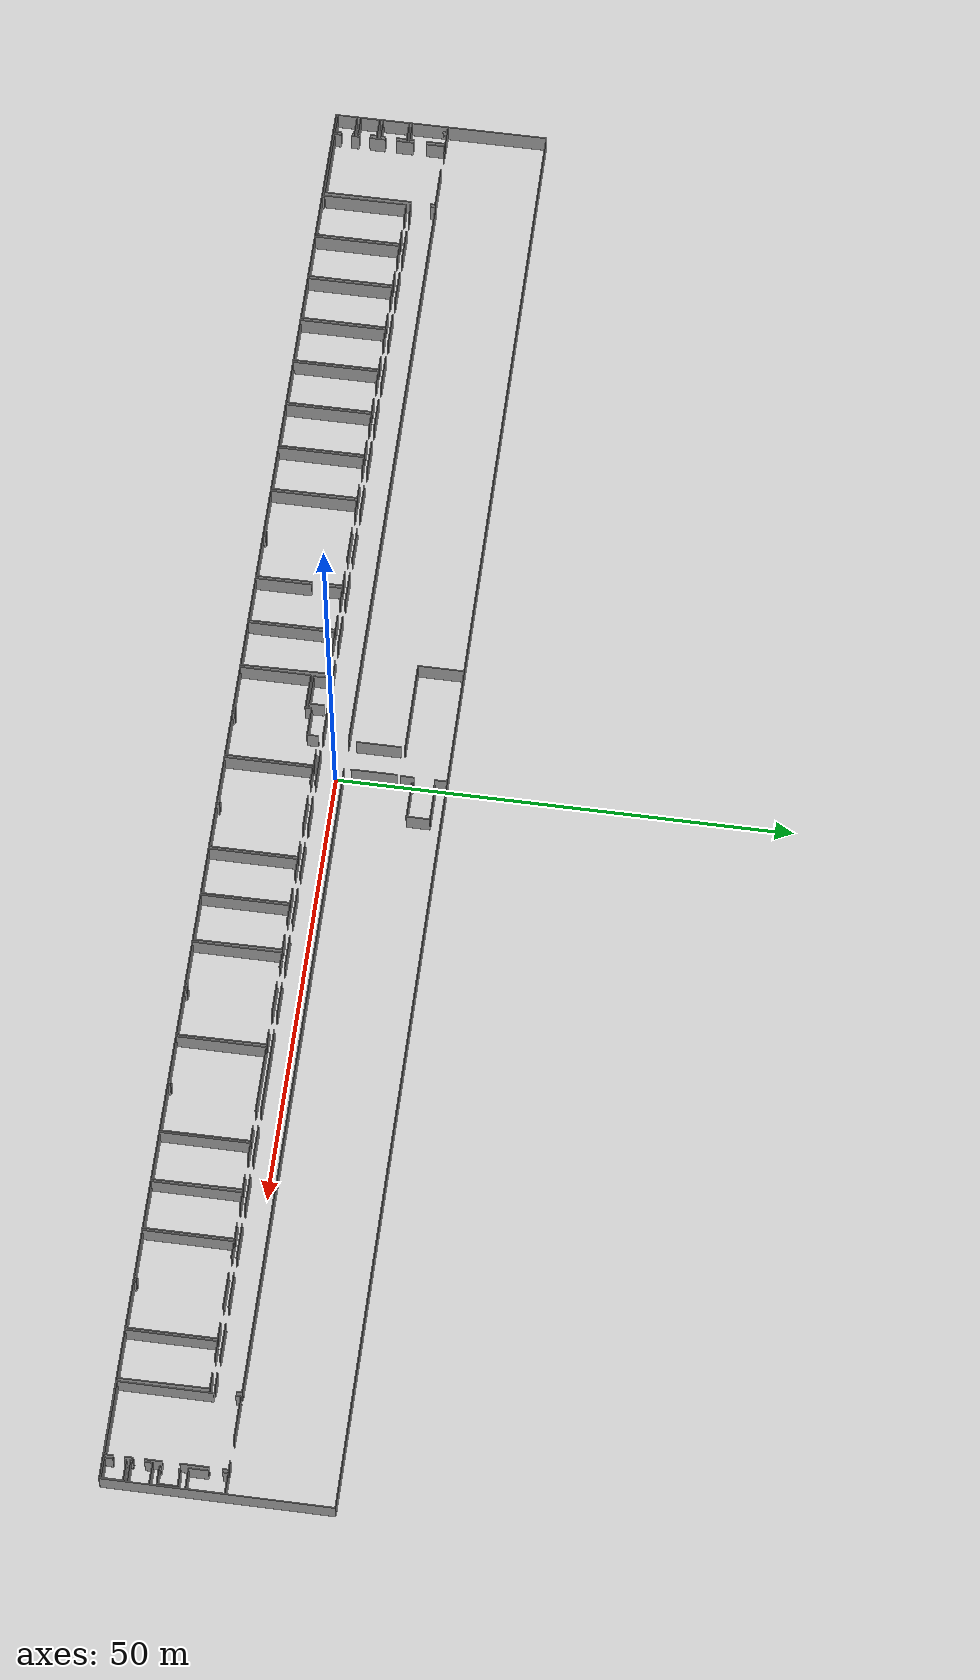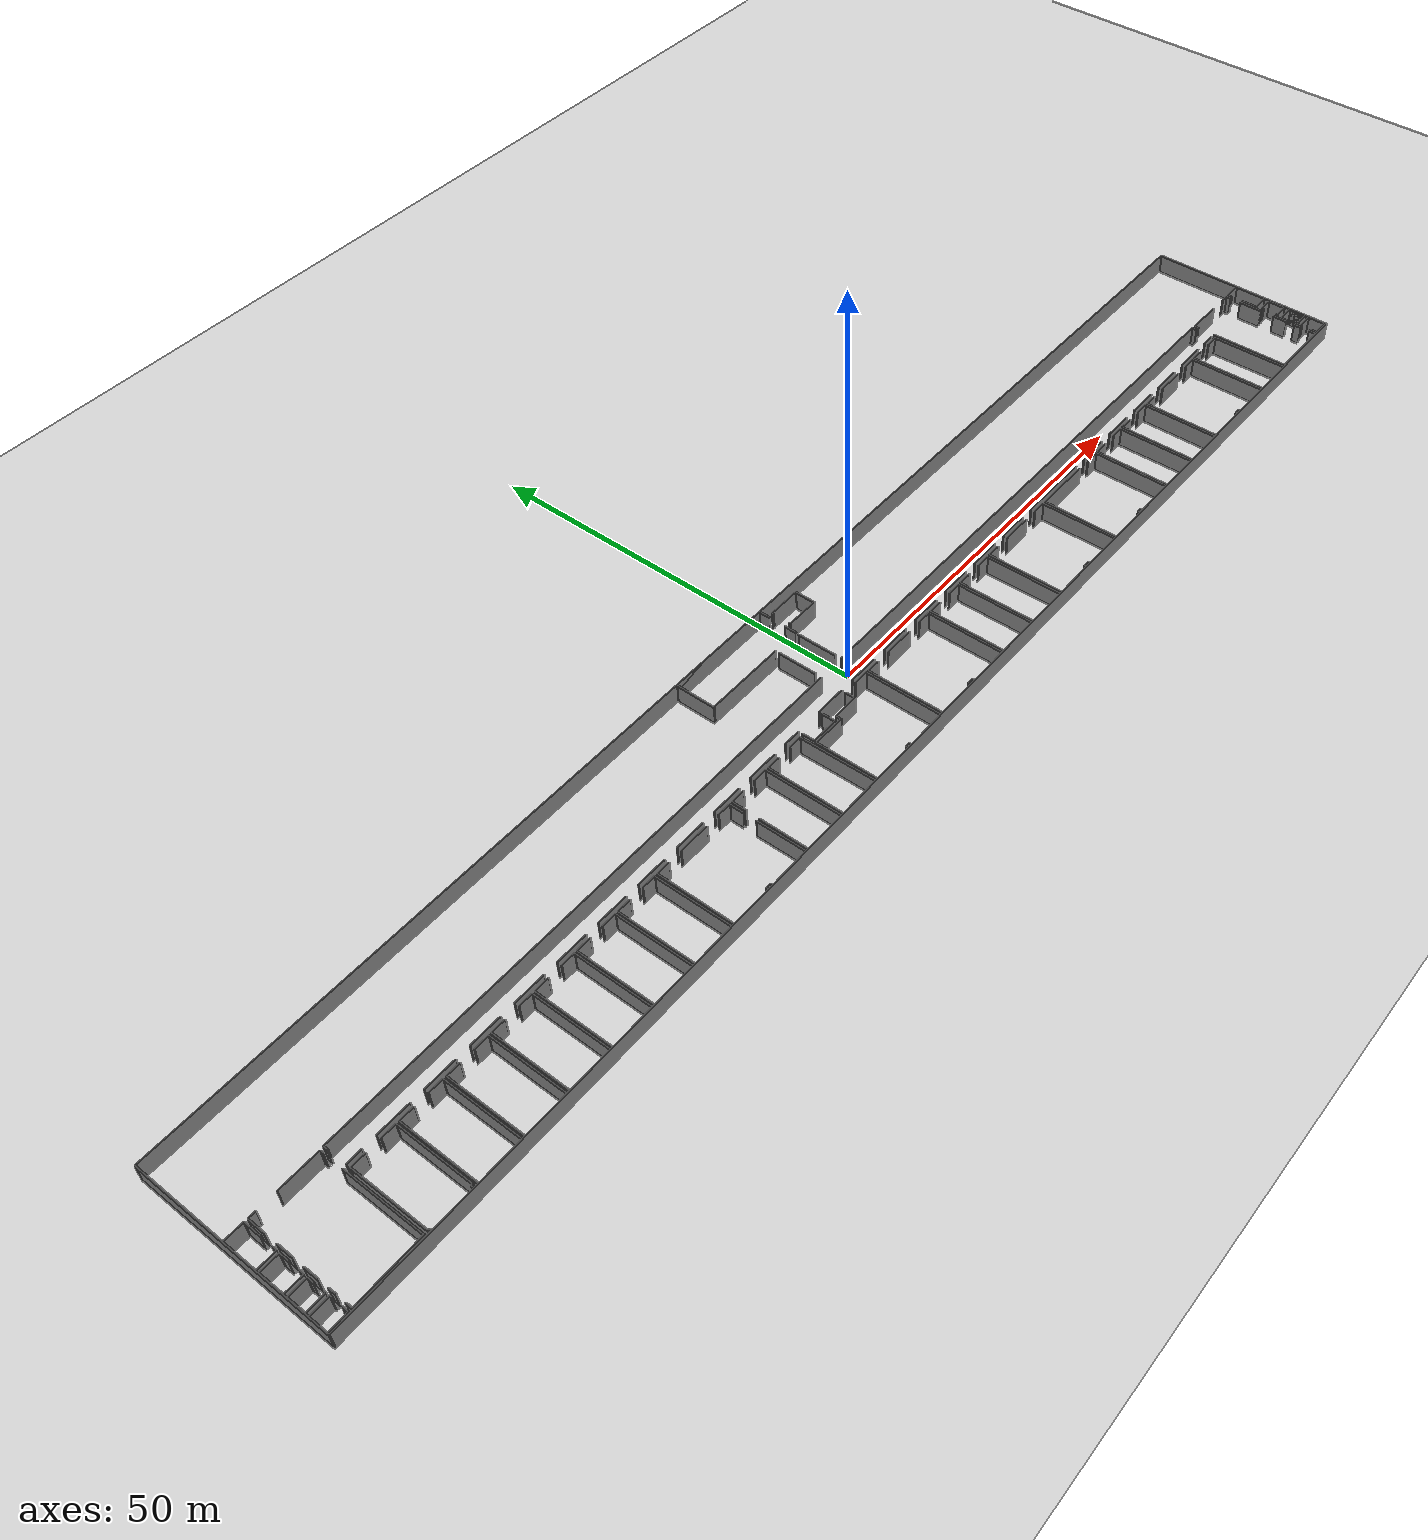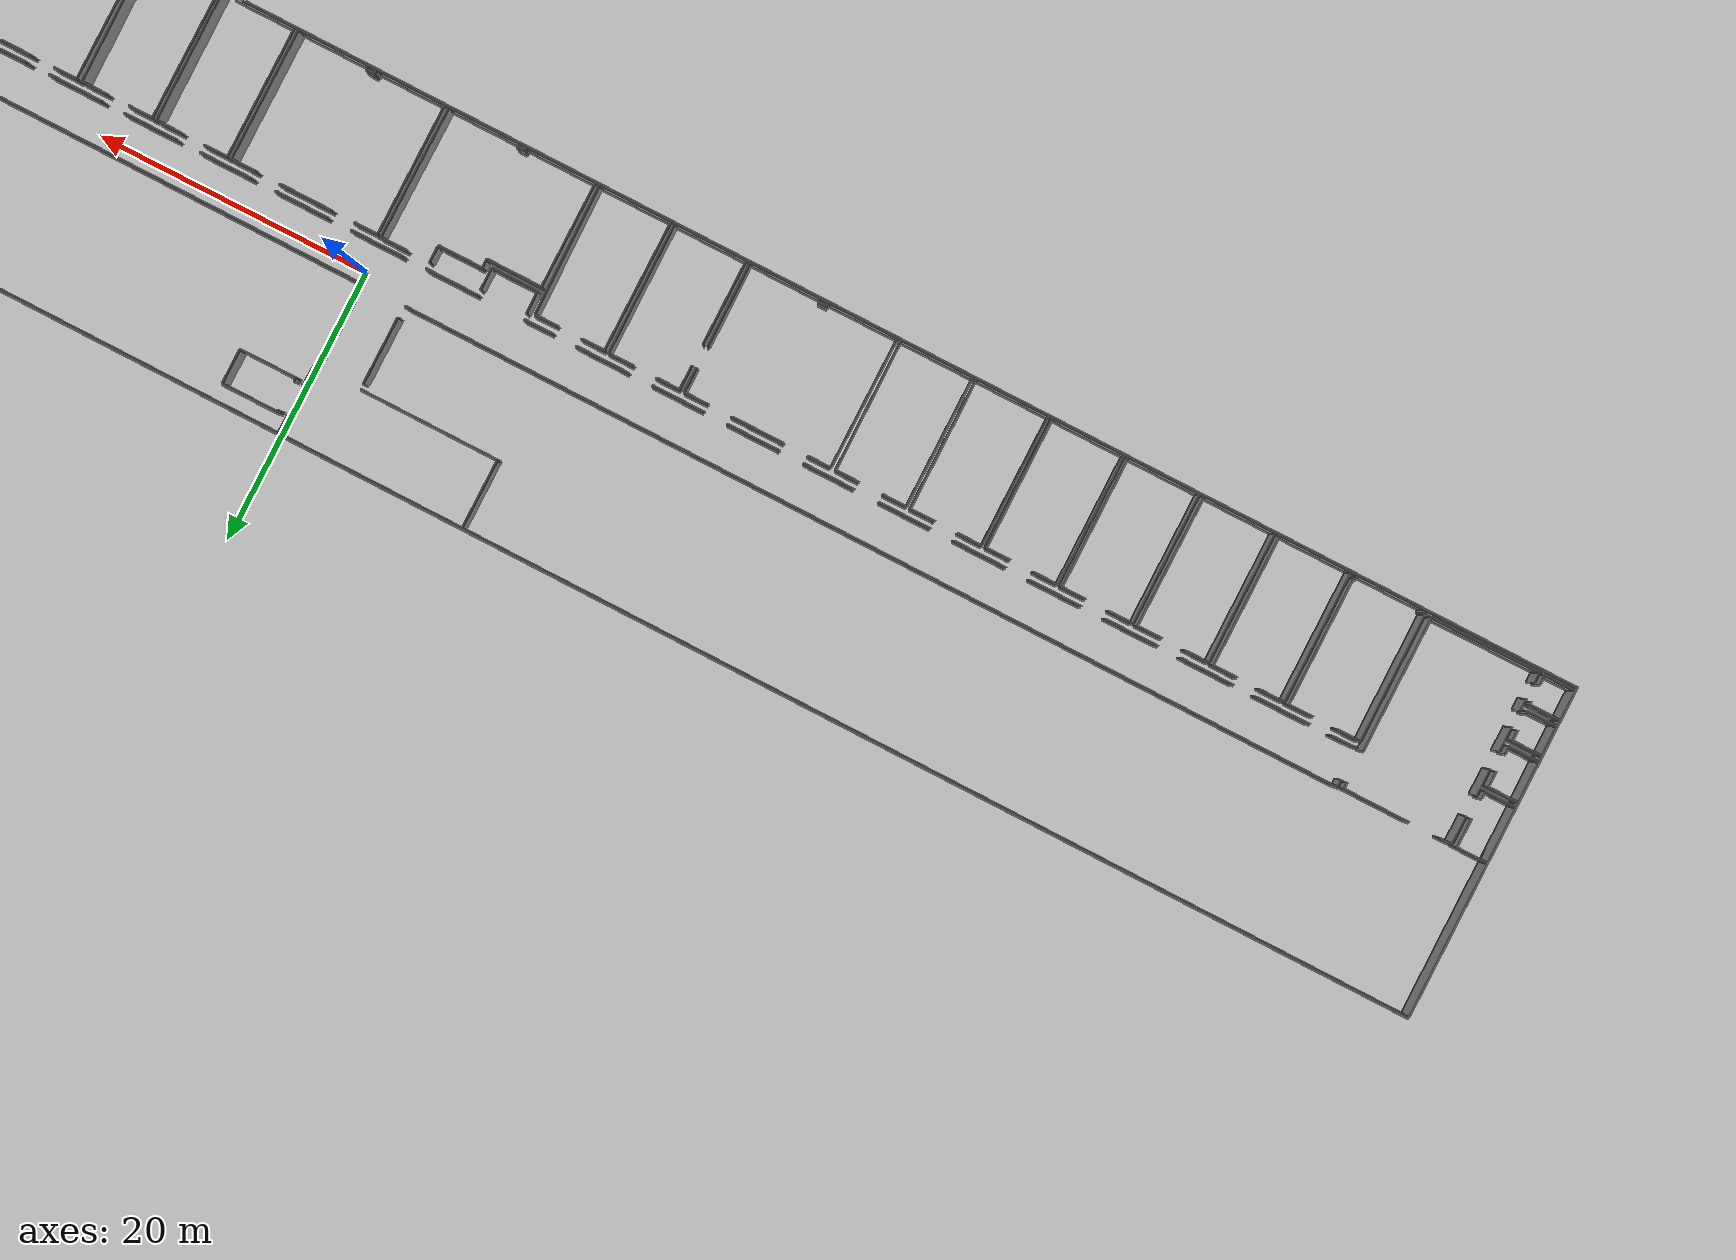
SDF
<sdf version="1.6">
  <world name="default">
    <light name="sun" type="directional">
      <cast_shadows>1</cast_shadows>
      <pose frame="">0 0 10 0 -0 0</pose>
      <diffuse>0.8 0.8 0.8 1</diffuse>
      <specular>0.1 0.1 0.1 1</specular>
      <attenuation>
        <range>1000</range>
        <constant>0.9</constant>
        <linear>0.01</linear>
        <quadratic>0.001</quadratic>
      </attenuation>
      <direction>-0.5 0.5 -1</direction>
    </light>
    <model name="ground_plane">
      <static>1</static>
      <link name="link">
        <collision name="collision">
          <geometry>
            <plane>
              <normal>0 0 1</normal>
              <size>100 100</size>
            </plane>
          </geometry>
          <surface>
            <friction>
              <ode>
                <mu>100</mu>
                <mu2>50</mu2>
              </ode>
              <torsional>
                <ode />
              </torsional>
            </friction>
            <contact>
              <ode />
            </contact>
            <bounce />
          </surface>
          <max_contacts>10</max_contacts>
        </collision>
        <visual name="visual">
          <cast_shadows>0</cast_shadows>
          <geometry>
            <plane>
              <normal>0 0 1</normal>
              <size>100 100</size>
            </plane>
          </geometry>
          <material>
            <script>
              <uri>file://media/materials/scripts/gazebo.material</uri>
              <name>Gazebo/Grey</name>
            </script>
          </material>
        </visual>
        <self_collide>0</self_collide>
        <kinematic>0</kinematic>
        <gravity>1</gravity>
      </link>
    </model>
    <gravity>0 0 -9.8</gravity>
    <magnetic_field>6e-06 2.3e-05 -4.2e-05</magnetic_field>
    <atmosphere type="adiabatic" />
    <physics default="0" name="default_physics" type="ode">
      <max_step_size>0.001</max_step_size>
      <real_time_factor>1</real_time_factor>
      <real_time_update_rate>1000</real_time_update_rate>
    </physics>
    <scene>
      <ambient>0.4 0.4 0.4 1</ambient>
      <background>0.7 0.7 0.7 1</background>
      <shadows>1</shadows>
    </scene>
    <spherical_coordinates>
      <surface_model>EARTH_WGS84</surface_model>
      <latitude_deg>0</latitude_deg>
      <longitude_deg>0</longitude_deg>
      <elevation>0</elevation>
      <heading_deg>0</heading_deg>
    </spherical_coordinates>
  <model name="0510045906_A_40_1_104">
		<static>1</static>
		<link name="Wall_0">
			<collision name="Wall_0_Collision">
				<geometry>
					<box>
						<size>0.55356292652 0.1 2.5</size>
					</box>
				</geometry>
				<pose frame="">0.27678146326 0 1.25 0 0 0</pose>
			</collision>
			<visual name="Wall_0_Visual">
				<pose frame="">0.27678146326 0 1.25 0 0 0</pose>
				<geometry>
					<box>
						<size>0.55356292652 0.1 2.5</size>
					</box>
				</geometry>
				<material>
					<script>
						<uri>file://media/materials/scripts/gazebo.material</uri>
						<name>Gazebo/Grey</name>
					</script>
					<ambient>1 1 1 1</ambient>
				</material>
			</visual>
			<pose frame="">11.0136168862 -11.8630058721 0 0 0 1.57079632679</pose>
		</link>
		<link name="Wall_1">
			<collision name="Wall_1_Collision">
				<geometry>
					<box>
						<size>69.0783050309 0.1 2.5</size>
					</box>
				</geometry>
				<pose frame="">34.5391525155 0 1.25 0 0 0</pose>
			</collision>
			<visual name="Wall_1_Visual">
				<pose frame="">34.5391525155 0 1.25 0 0 0</pose>
				<geometry>
					<box>
						<size>69.0783050309 0.1 2.5</size>
					</box>
				</geometry>
				<material>
					<script>
						<uri>file://media/materials/scripts/gazebo.material</uri>
						<name>Gazebo/Grey</name>
					</script>
					<ambient>1 1 1 1</ambient>
				</material>
			</visual>
			<pose frame="">11.0136168862 -11.3094429456 0 0 0 0.0</pose>
		</link>
		<link name="Wall_2">
			<collision name="Wall_2_Collision">
				<geometry>
					<box>
						<size>72.7622916997 0.1 2.5</size>
					</box>
				</geometry>
				<pose frame="">36.3811458499 0 1.25 0 0 0</pose>
			</collision>
			<visual name="Wall_2_Visual">
				<pose frame="">36.3811458499 0 1.25 0 0 0</pose>
				<geometry>
					<box>
						<size>72.7622916997 0.1 2.5</size>
					</box>
				</geometry>
				<material>
					<script>
						<uri>file://media/materials/scripts/gazebo.material</uri>
						<name>Gazebo/Grey</name>
					</script>
					<ambient>1 1 1 1</ambient>
				</material>
			</visual>
			<pose frame="">83.4841453738 -11.3094429456 0 0 0 0.0</pose>
		</link>
		<link name="Wall_3">
			<collision name="Wall_3_Collision">
				<geometry>
					<box>
						<size>0.60663386764 0.1 2.5</size>
					</box>
				</geometry>
				<pose frame="">0.30331693382 0 1.25 0 0 0</pose>
			</collision>
			<visual name="Wall_3_Visual">
				<pose frame="">0.30331693382 0 1.25 0 0 0</pose>
				<geometry>
					<box>
						<size>0.60663386764 0.1 2.5</size>
					</box>
				</geometry>
				<material>
					<script>
						<uri>file://media/materials/scripts/gazebo.material</uri>
						<name>Gazebo/Grey</name>
					</script>
					<ambient>1 1 1 1</ambient>
				</material>
			</visual>
			<pose frame="">156.246437073 -11.3094429456 0 0 0 -1.57079632679</pose>
		</link>
		<link name="Wall_4">
			<collision name="Wall_4_Collision">
				<geometry>
					<box>
						<size>1.79323916839 0.1 2.5</size>
					</box>
				</geometry>
				<pose frame="">0.896619584193 0 1.25 0 0 0</pose>
			</collision>
			<visual name="Wall_4_Visual">
				<pose frame="">0.896619584193 0 1.25 0 0 0</pose>
				<geometry>
					<box>
						<size>1.79323916839 0.1 2.5</size>
					</box>
				</geometry>
				<material>
					<script>
						<uri>file://media/materials/scripts/gazebo.material</uri>
						<name>Gazebo/Grey</name>
					</script>
					<ambient>1 1 1 1</ambient>
				</material>
			</visual>
			<pose frame="">156.246437073 -14.1445484844 0 0 0 3.14159265359</pose>
		</link>
		<link name="Wall_5">
			<collision name="Wall_5_Collision">
				<geometry>
					<box>
						<size>3.86351372798 0.1 2.5</size>
					</box>
				</geometry>
				<pose frame="">1.93175686399 0 1.25 0 0 0</pose>
			</collision>
			<visual name="Wall_5_Visual">
				<pose frame="">1.93175686399 0 1.25 0 0 0</pose>
				<geometry>
					<box>
						<size>3.86351372798 0.1 2.5</size>
					</box>
				</geometry>
				<material>
					<script>
						<uri>file://media/materials/scripts/gazebo.material</uri>
						<name>Gazebo/Grey</name>
					</script>
					<ambient>1 1 1 1</ambient>
				</material>
			</visual>
			<pose frame="">152.813585145 -14.1445484844 0 0 0 3.14159265359</pose>
		</link>
		<link name="Wall_6">
			<collision name="Wall_6_Collision">
				<geometry>
					<box>
						<size>3.82186954452 0.1 2.5</size>
					</box>
				</geometry>
				<pose frame="">1.91093477226 0 1.25 0 0 0</pose>
			</collision>
			<visual name="Wall_6_Visual">
				<pose frame="">1.91093477226 0 1.25 0 0 0</pose>
				<geometry>
					<box>
						<size>3.82186954452 0.1 2.5</size>
					</box>
				</geometry>
				<material>
					<script>
						<uri>file://media/materials/scripts/gazebo.material</uri>
						<name>Gazebo/Grey</name>
					</script>
					<ambient>1 1 1 1</ambient>
				</material>
			</visual>
			<pose frame="">147.115695921 -14.1445484844 0 0 0 3.14159265359</pose>
		</link>
		<link name="Wall_7">
			<collision name="Wall_7_Collision">
				<geometry>
					<box>
						<size>3.92344072369 0.1 2.5</size>
					</box>
				</geometry>
				<pose frame="">1.96172036185 0 1.25 0 0 0</pose>
			</collision>
			<visual name="Wall_7_Visual">
				<pose frame="">1.96172036185 0 1.25 0 0 0</pose>
				<geometry>
					<box>
						<size>3.92344072369 0.1 2.5</size>
					</box>
				</geometry>
				<material>
					<script>
						<uri>file://media/materials/scripts/gazebo.material</uri>
						<name>Gazebo/Grey</name>
					</script>
					<ambient>1 1 1 1</ambient>
				</material>
			</visual>
			<pose frame="">141.623234407 -14.1445484844 0 0 0 3.14159265359</pose>
		</link>
		<link name="Wall_8">
			<collision name="Wall_8_Collision">
				<geometry>
					<box>
						<size>3.90541183939 0.1 2.5</size>
					</box>
				</geometry>
				<pose frame="">1.9527059197 0 1.25 0 0 0</pose>
			</collision>
			<visual name="Wall_8_Visual">
				<pose frame="">1.9527059197 0 1.25 0 0 0</pose>
				<geometry>
					<box>
						<size>3.90541183939 0.1 2.5</size>
					</box>
				</geometry>
				<material>
					<script>
						<uri>file://media/materials/scripts/gazebo.material</uri>
						<name>Gazebo/Grey</name>
					</script>
					<ambient>1 1 1 1</ambient>
				</material>
			</visual>
			<pose frame="">136.024631011 -14.1445484844 0 0 0 3.14159265359</pose>
		</link>
		<link name="Wall_9">
			<collision name="Wall_9_Collision">
				<geometry>
					<box>
						<size>3.90109506428 0.1 2.5</size>
					</box>
				</geometry>
				<pose frame="">1.95054753214 0 1.25 0 0 0</pose>
			</collision>
			<visual name="Wall_9_Visual">
				<pose frame="">1.95054753214 0 1.25 0 0 0</pose>
				<geometry>
					<box>
						<size>3.90109506428 0.1 2.5</size>
					</box>
				</geometry>
				<material>
					<script>
						<uri>file://media/materials/scripts/gazebo.material</uri>
						<name>Gazebo/Grey</name>
					</script>
					<ambient>1 1 1 1</ambient>
				</material>
			</visual>
			<pose frame="">130.392255198 -14.1445484844 0 0 0 3.14159265359</pose>
		</link>
		<link name="Wall_10">
			<collision name="Wall_10_Collision">
				<geometry>
					<box>
						<size>9.49360418981 0.1 2.5</size>
					</box>
				</geometry>
				<pose frame="">4.74680209491 0 1.25 0 0 0</pose>
			</collision>
			<visual name="Wall_10_Visual">
				<pose frame="">4.74680209491 0 1.25 0 0 0</pose>
				<geometry>
					<box>
						<size>9.49360418981 0.1 2.5</size>
					</box>
				</geometry>
				<material>
					<script>
						<uri>file://media/materials/scripts/gazebo.material</uri>
						<name>Gazebo/Grey</name>
					</script>
					<ambient>1 1 1 1</ambient>
				</material>
			</visual>
			<pose frame="">124.816505317 -14.1445484844 0 0 0 3.14159265359</pose>
		</link>
		<link name="Wall_11">
			<collision name="Wall_11_Collision">
				<geometry>
					<box>
						<size>3.85183304237 0.1 2.5</size>
					</box>
				</geometry>
				<pose frame="">1.92591652119 0 1.25 0 0 0</pose>
			</collision>
			<visual name="Wall_11_Visual">
				<pose frame="">1.92591652119 0 1.25 0 0 0</pose>
				<geometry>
					<box>
						<size>3.85183304237 0.1 2.5</size>
					</box>
				</geometry>
				<material>
					<script>
						<uri>file://media/materials/scripts/gazebo.material</uri>
						<name>Gazebo/Grey</name>
					</script>
					<ambient>1 1 1 1</ambient>
				</material>
			</visual>
			<pose frame="">113.57156007 -14.1445484844 0 0 0 3.14159265359</pose>
		</link>
		<link name="Wall_12">
			<collision name="Wall_12_Collision">
				<geometry>
					<box>
						<size>3.91379146167 0.1 2.5</size>
					</box>
				</geometry>
				<pose frame="">1.95689573084 0 1.25 0 0 0</pose>
			</collision>
			<visual name="Wall_12_Visual">
				<pose frame="">1.95689573084 0 1.25 0 0 0</pose>
				<geometry>
					<box>
						<size>3.91379146167 0.1 2.5</size>
					</box>
				</geometry>
				<material>
					<script>
						<uri>file://media/materials/scripts/gazebo.material</uri>
						<name>Gazebo/Grey</name>
					</script>
					<ambient>1 1 1 1</ambient>
				</material>
			</visual>
			<pose frame="">108.021202984 -14.1445484844 0 0 0 3.14159265359</pose>
		</link>
		<link name="Wall_13">
			<collision name="Wall_13_Collision">
				<geometry>
					<box>
						<size>3.86173623234 0.1 2.5</size>
					</box>
				</geometry>
				<pose frame="">1.93086811617 0 1.25 0 0 0</pose>
			</collision>
			<visual name="Wall_13_Visual">
				<pose frame="">1.93086811617 0 1.25 0 0 0</pose>
				<geometry>
					<box>
						<size>3.86173623234 0.1 2.5</size>
					</box>
				</geometry>
				<material>
					<script>
						<uri>file://media/materials/scripts/gazebo.material</uri>
						<name>Gazebo/Grey</name>
					</script>
					<ambient>1 1 1 1</ambient>
				</material>
			</visual>
			<pose frame="">102.414473893 -14.1445484844 0 0 0 3.14159265359</pose>
		</link>
		<link name="Wall_14">
			<collision name="Wall_14_Collision">
				<geometry>
					<box>
						<size>3.8117124266 0.1 2.5</size>
					</box>
				</geometry>
				<pose frame="">1.9058562133 0 1.25 0 0 0</pose>
			</collision>
			<visual name="Wall_14_Visual">
				<pose frame="">1.9058562133 0 1.25 0 0 0</pose>
				<geometry>
					<box>
						<size>3.8117124266 0.1 2.5</size>
					</box>
				</geometry>
				<material>
					<script>
						<uri>file://media/materials/scripts/gazebo.material</uri>
						<name>Gazebo/Grey</name>
					</script>
					<ambient>1 1 1 1</ambient>
				</material>
			</visual>
			<pose frame="">96.7785430884 -14.1445484844 0 0 0 3.14159265359</pose>
		</link>
		<link name="Wall_15">
			<collision name="Wall_15_Collision">
				<geometry>
					<box>
						<size>3.86605300746 0.1 2.5</size>
					</box>
				</geometry>
				<pose frame="">1.93302650373 0 1.25 0 0 0</pose>
			</collision>
			<visual name="Wall_15_Visual">
				<pose frame="">1.93302650373 0 1.25 0 0 0</pose>
				<geometry>
					<box>
						<size>3.86605300746 0.1 2.5</size>
					</box>
				</geometry>
				<material>
					<script>
						<uri>file://media/materials/scripts/gazebo.material</uri>
						<name>Gazebo/Grey</name>
					</script>
					<ambient>1 1 1 1</ambient>
				</material>
			</visual>
			<pose frame="">91.1817171877 -14.1445484844 0 0 0 3.14159265359</pose>
		</link>
		<link name="Wall_16">
			<collision name="Wall_16_Collision">
				<geometry>
					<box>
						<size>3.89728614506 0.1 2.5</size>
					</box>
				</geometry>
				<pose frame="">1.94864307253 0 1.25 0 0 0</pose>
			</collision>
			<visual name="Wall_16_Visual">
				<pose frame="">1.94864307253 0 1.25 0 0 0</pose>
				<geometry>
					<box>
						<size>3.89728614506 0.1 2.5</size>
					</box>
				</geometry>
				<material>
					<script>
						<uri>file://media/materials/scripts/gazebo.material</uri>
						<name>Gazebo/Grey</name>
					</script>
					<ambient>1 1 1 1</ambient>
				</material>
			</visual>
			<pose frame="">85.5701634661 -14.1445484844 0 0 0 3.14159265359</pose>
		</link>
		<link name="Wall_17">
			<collision name="Wall_17_Collision">
				<geometry>
					<box>
						<size>3.87519441359 0.1 2.5</size>
					</box>
				</geometry>
				<pose frame="">1.93759720679 0 1.25 0 0 0</pose>
			</collision>
			<visual name="Wall_17_Visual">
				<pose frame="">1.93759720679 0 1.25 0 0 0</pose>
				<geometry>
					<box>
						<size>3.87519441359 0.1 2.5</size>
					</box>
				</geometry>
				<material>
					<script>
						<uri>file://media/materials/scripts/gazebo.material</uri>
						<name>Gazebo/Grey</name>
					</script>
					<ambient>1 1 1 1</ambient>
				</material>
			</visual>
			<pose frame="">79.9822250436 -14.1445484844 0 0 0 3.14159265359</pose>
		</link>
		<link name="Wall_18">
			<collision name="Wall_18_Collision">
				<geometry>
					<box>
						<size>2.12106014918 0.1 2.5</size>
					</box>
				</geometry>
				<pose frame="">1.06053007459 0 1.25 0 0 0</pose>
			</collision>
			<visual name="Wall_18_Visual">
				<pose frame="">1.06053007459 0 1.25 0 0 0</pose>
				<geometry>
					<box>
						<size>2.12106014918 0.1 2.5</size>
					</box>
				</geometry>
				<material>
					<script>
						<uri>file://media/materials/scripts/gazebo.material</uri>
						<name>Gazebo/Grey</name>
					</script>
					<ambient>1 1 1 1</ambient>
				</material>
			</visual>
			<pose frame="">72.6594508808 -14.1445484844 0 0 0 3.14159265359</pose>
		</link>
		<link name="Wall_19">
			<collision name="Wall_19_Collision">
				<geometry>
					<box>
						<size>3.90236470402 0.1 2.5</size>
					</box>
				</geometry>
				<pose frame="">1.95118235201 0 1.25 0 0 0</pose>
			</collision>
			<visual name="Wall_19_Visual">
				<pose frame="">1.95118235201 0 1.25 0 0 0</pose>
				<geometry>
					<box>
						<size>3.90236470402 0.1 2.5</size>
					</box>
				</geometry>
				<material>
					<script>
						<uri>file://media/materials/scripts/gazebo.material</uri>
						<name>Gazebo/Grey</name>
					</script>
					<ambient>1 1 1 1</ambient>
				</material>
			</visual>
			<pose frame="">68.8479923822 -14.1445484844 0 0 0 3.14159265359</pose>
		</link>
		<link name="Wall_20">
			<collision name="Wall_20_Collision">
				<geometry>
					<box>
						<size>3.81272813839 0.1 2.5</size>
					</box>
				</geometry>
				<pose frame="">1.9063640692 0 1.25 0 0 0</pose>
			</collision>
			<visual name="Wall_20_Visual">
				<pose frame="">1.9063640692 0 1.25 0 0 0</pose>
				<geometry>
					<box>
						<size>3.81272813839 0.1 2.5</size>
					</box>
				</geometry>
				<material>
					<script>
						<uri>file://media/materials/scripts/gazebo.material</uri>
						<name>Gazebo/Grey</name>
					</script>
					<ambient>1 1 1 1</ambient>
				</material>
			</visual>
			<pose frame="">63.1782891605 -14.1445484844 0 0 0 3.14159265359</pose>
		</link>
		<link name="Wall_21">
			<collision name="Wall_21_Collision">
				<geometry>
					<box>
						<size>3.87341691795 0.1 2.5</size>
					</box>
				</geometry>
				<pose frame="">1.93670845897 0 1.25 0 0 0</pose>
			</collision>
			<visual name="Wall_21_Visual">
				<pose frame="">1.93670845897 0 1.25 0 0 0</pose>
				<geometry>
					<box>
						<size>3.87341691795 0.1 2.5</size>
					</box>
				</geometry>
				<material>
					<script>
						<uri>file://media/materials/scripts/gazebo.material</uri>
						<name>Gazebo/Grey</name>
					</script>
					<ambient>1 1 1 1</ambient>
				</material>
			</visual>
			<pose frame="">57.6401206158 -14.1445484844 0 0 0 3.14159265359</pose>
		</link>
		<link name="Wall_22">
			<collision name="Wall_22_Collision">
				<geometry>
					<box>
						<size>3.79825424536 0.1 2.5</size>
					</box>
				</geometry>
				<pose frame="">1.89912712268 0 1.25 0 0 0</pose>
			</collision>
			<visual name="Wall_22_Visual">
				<pose frame="">1.89912712268 0 1.25 0 0 0</pose>
				<geometry>
					<box>
						<size>3.79825424536 0.1 2.5</size>
					</box>
				</geometry>
				<material>
					<script>
						<uri>file://media/materials/scripts/gazebo.material</uri>
						<name>Gazebo/Grey</name>
					</script>
					<ambient>1 1 1 1</ambient>
				</material>
			</visual>
			<pose frame="">51.9772734487 -14.1445484844 0 0 0 3.14159265359</pose>
		</link>
		<link name="Wall_23">
			<collision name="Wall_23_Collision">
				<geometry>
					<box>
						<size>3.86427551182 0.1 2.5</size>
					</box>
				</geometry>
				<pose frame="">1.93213775591 0 1.25 0 0 0</pose>
			</collision>
			<visual name="Wall_23_Visual">
				<pose frame="">1.93213775591 0 1.25 0 0 0</pose>
				<geometry>
					<box>
						<size>3.86427551182 0.1 2.5</size>
					</box>
				</geometry>
				<material>
					<script>
						<uri>file://media/materials/scripts/gazebo.material</uri>
						<name>Gazebo/Grey</name>
					</script>
					<ambient>1 1 1 1</ambient>
				</material>
			</visual>
			<pose frame="">46.4005078559 -14.1445484844 0 0 0 3.14159265359</pose>
		</link>
		<link name="Wall_24">
			<collision name="Wall_24_Collision">
				<geometry>
					<box>
						<size>3.91252182193 0.1 2.5</size>
					</box>
				</geometry>
				<pose frame="">1.95626091097 0 1.25 0 0 0</pose>
			</collision>
			<visual name="Wall_24_Visual">
				<pose frame="">1.95626091097 0 1.25 0 0 0</pose>
				<geometry>
					<box>
						<size>3.91252182193 0.1 2.5</size>
					</box>
				</geometry>
				<material>
					<script>
						<uri>file://media/materials/scripts/gazebo.material</uri>
						<name>Gazebo/Grey</name>
					</script>
					<ambient>1 1 1 1</ambient>
				</material>
			</visual>
			<pose frame="">40.8564989684 -14.1445484844 0 0 0 3.14159265359</pose>
		</link>
		<link name="Wall_25">
			<collision name="Wall_25_Collision">
				<geometry>
					<box>
						<size>3.88306617997 0.1 2.5</size>
					</box>
				</geometry>
				<pose frame="">1.94153308999 0 1.25 0 0 0</pose>
			</collision>
			<visual name="Wall_25_Visual">
				<pose frame="">1.94153308999 0 1.25 0 0 0</pose>
				<geometry>
					<box>
						<size>3.88306617997 0.1 2.5</size>
					</box>
				</geometry>
				<material>
					<script>
						<uri>file://media/materials/scripts/gazebo.material</uri>
						<name>Gazebo/Grey</name>
					</script>
					<ambient>1 1 1 1</ambient>
				</material>
			</visual>
			<pose frame="">35.2469766704 -14.1445484844 0 0 0 3.14159265359</pose>
		</link>
		<link name="Wall_26">
			<collision name="Wall_26_Collision">
				<geometry>
					<box>
						<size>3.89906364069 0.1 2.5</size>
					</box>
				</geometry>
				<pose frame="">1.94953182035 0 1.25 0 0 0</pose>
			</collision>
			<visual name="Wall_26_Visual">
				<pose frame="">1.94953182035 0 1.25 0 0 0</pose>
				<geometry>
					<box>
						<size>3.89906364069 0.1 2.5</size>
					</box>
				</geometry>
				<material>
					<script>
						<uri>file://media/materials/scripts/gazebo.material</uri>
						<name>Gazebo/Grey</name>
					</script>
					<ambient>1 1 1 1</ambient>
				</material>
			</visual>
			<pose frame="">29.6072369465 -14.1445484844 0 0 0 3.14159265359</pose>
		</link>
		<link name="Wall_27">
			<collision name="Wall_27_Collision">
				<geometry>
					<box>
						<size>3.88636724329 0.1 2.5</size>
					</box>
				</geometry>
				<pose frame="">1.94318362165 0 1.25 0 0 0</pose>
			</collision>
			<visual name="Wall_27_Visual">
				<pose frame="">1.94318362165 0 1.25 0 0 0</pose>
				<geometry>
					<box>
						<size>3.88636724329 0.1 2.5</size>
					</box>
				</geometry>
				<material>
					<script>
						<uri>file://media/materials/scripts/gazebo.material</uri>
						<name>Gazebo/Grey</name>
					</script>
					<ambient>1 1 1 1</ambient>
				</material>
			</visual>
			<pose frame="">24.0165053166 -14.1445484844 0 0 0 3.14159265359</pose>
		</link>
		<link name="Wall_28">
			<collision name="Wall_28_Collision">
				<geometry>
					<box>
						<size>3.9780352325 0.1 2.5</size>
					</box>
				</geometry>
				<pose frame="">1.98901761625 0 1.25 0 0 0</pose>
			</collision>
			<visual name="Wall_28_Visual">
				<pose frame="">1.98901761625 0 1.25 0 0 0</pose>
				<geometry>
					<box>
						<size>3.9780352325 0.1 2.5</size>
					</box>
				</geometry>
				<material>
					<script>
						<uri>file://media/materials/scripts/gazebo.material</uri>
						<name>Gazebo/Grey</name>
					</script>
					<ambient>1 1 1 1</ambient>
				</material>
			</visual>
			<pose frame="">18.4836692588 -14.1445484844 0 0 0 3.14159265359</pose>
		</link>
		<link name="Wall_29">
			<collision name="Wall_29_Collision">
				<geometry>
					<box>
						<size>1.85124250872 0.1 2.5</size>
					</box>
				</geometry>
				<pose frame="">0.92562125436 0 1.25 0 0 0</pose>
			</collision>
			<visual name="Wall_29_Visual">
				<pose frame="">0.92562125436 0 1.25 0 0 0</pose>
				<geometry>
					<box>
						<size>1.85124250872 0.1 2.5</size>
					</box>
				</geometry>
				<material>
					<script>
						<uri>file://media/materials/scripts/gazebo.material</uri>
						<name>Gazebo/Grey</name>
					</script>
					<ambient>1 1 1 1</ambient>
				</material>
			</visual>
			<pose frame="">12.8642437708 -14.1445484844 0 0 0 -3.11580254427</pose>
		</link>
		<link name="Wall_30">
			<collision name="Wall_30_Collision">
				<geometry>
					<box>
						<size>0.795302332963 0.1 2.5</size>
					</box>
				</geometry>
				<pose frame="">0.397651166482 0 1.25 0 0 0</pose>
			</collision>
			<visual name="Wall_30_Visual">
				<pose frame="">0.397651166482 0 1.25 0 0 0</pose>
				<geometry>
					<box>
						<size>0.795302332963 0.1 2.5</size>
					</box>
				</geometry>
				<material>
					<script>
						<uri>file://media/materials/scripts/gazebo.material</uri>
						<name>Gazebo/Grey</name>
					</script>
					<ambient>1 1 1 1</ambient>
				</material>
			</visual>
			<pose frame="">2.63018568481 -24.15591176 0 0 0 1.57079632679</pose>
		</link>
		<link name="Wall_31">
			<collision name="Wall_31_Collision">
				<geometry>
					<box>
						<size>0.900174575464 0.1 2.5</size>
					</box>
				</geometry>
				<pose frame="">0.450087287732 0 1.25 0 0 0</pose>
			</collision>
			<visual name="Wall_31_Visual">
				<pose frame="">0.450087287732 0 1.25 0 0 0</pose>
				<geometry>
					<box>
						<size>0.900174575464 0.1 2.5</size>
					</box>
				</geometry>
				<material>
					<script>
						<uri>file://media/materials/scripts/gazebo.material</uri>
						<name>Gazebo/Grey</name>
					</script>
					<ambient>1 1 1 1</ambient>
				</material>
			</visual>
			<pose frame="">2.63018568481 -22.1841612442 0 0 0 1.57079632679</pose>
		</link>
		<link name="Wall_32">
			<collision name="Wall_32_Collision">
				<geometry>
					<box>
						<size>1.81126805269 0.1 2.5</size>
					</box>
				</geometry>
				<pose frame="">0.905634026345 0 1.25 0 0 0</pose>
			</collision>
			<visual name="Wall_32_Visual">
				<pose frame="">0.905634026345 0 1.25 0 0 0</pose>
				<geometry>
					<box>
						<size>1.81126805269 0.1 2.5</size>
					</box>
				</geometry>
				<material>
					<script>
						<uri>file://media/materials/scripts/gazebo.material</uri>
						<name>Gazebo/Grey</name>
					</script>
					<ambient>1 1 1 1</ambient>
				</material>
			</visual>
			<pose frame="">2.63018568481 -20.0836692588 0 0 0 1.57079632679</pose>
		</link>
		<link name="Wall_33">
			<collision name="Wall_33_Collision">
				<geometry>
					<box>
						<size>1.98724012062 0.1 2.5</size>
					</box>
				</geometry>
				<pose frame="">0.993620060308 0 1.25 0 0 0</pose>
			</collision>
			<visual name="Wall_33_Visual">
				<pose frame="">0.993620060308 0 1.25 0 0 0</pose>
				<geometry>
					<box>
						<size>1.98724012062 0.1 2.5</size>
					</box>
				</geometry>
				<material>
					<script>
						<uri>file://media/materials/scripts/gazebo.material</uri>
						<name>Gazebo/Grey</name>
					</script>
					<ambient>1 1 1 1</ambient>
				</material>
			</visual>
			<pose frame="">2.63018568481 -16.9880336455 0 0 0 1.57079632679</pose>
		</link>
		<link name="Wall_34">
			<collision name="Wall_34_Collision">
				<geometry>
					<box>
						<size>2.10785589589 0.1 2.5</size>
					</box>
				</geometry>
				<pose frame="">1.05392794794 0 1.25 0 0 0</pose>
			</collision>
			<visual name="Wall_34_Visual">
				<pose frame="">1.05392794794 0 1.25 0 0 0</pose>
				<geometry>
					<box>
						<size>2.10785589589 0.1 2.5</size>
					</box>
				</geometry>
				<material>
					<script>
						<uri>file://media/materials/scripts/gazebo.material</uri>
						<name>Gazebo/Grey</name>
					</script>
					<ambient>1 1 1 1</ambient>
				</material>
			</visual>
			<pose frame="">2.63018568481 -13.5188700206 0 0 0 1.57079632679</pose>
		</link>
		<link name="Wall_35">
			<collision name="Wall_35_Collision">
				<geometry>
					<box>
						<size>0.868433581971 0.1 2.5</size>
					</box>
				</geometry>
				<pose frame="">0.434216790986 0 1.25 0 0 0</pose>
			</collision>
			<visual name="Wall_35_Visual">
				<pose frame="">0.434216790986 0 1.25 0 0 0</pose>
				<geometry>
					<box>
						<size>0.868433581971 0.1 2.5</size>
					</box>
				</geometry>
				<material>
					<script>
						<uri>file://media/materials/scripts/gazebo.material</uri>
						<name>Gazebo/Grey</name>
					</script>
					<ambient>1 1 1 1</ambient>
				</material>
			</visual>
			<pose frame="">2.63018568481 -11.4110141247 0 0 0 0.0</pose>
		</link>
		<link name="Wall_36">
			<collision name="Wall_36_Collision">
				<geometry>
					<box>
						<size>4.80837962228 0.1 2.5</size>
					</box>
				</geometry>
				<pose frame="">2.40418981114 0 1.25 0 0 0</pose>
			</collision>
			<visual name="Wall_36_Visual">
				<pose frame="">2.40418981114 0 1.25 0 0 0</pose>
				<geometry>
					<box>
						<size>4.80837962228 0.1 2.5</size>
					</box>
				</geometry>
				<material>
					<script>
						<uri>file://media/materials/scripts/gazebo.material</uri>
						<name>Gazebo/Grey</name>
					</script>
					<ambient>1 1 1 1</ambient>
				</material>
			</visual>
			<pose frame="">5.79285827646 -11.4110141247 0 0 0 0.0</pose>
		</link>
		<link name="Wall_37">
			<collision name="Wall_37_Collision">
				<geometry>
					<box>
						<size>0.483224884939 0.1 2.5</size>
					</box>
				</geometry>
				<pose frame="">0.241612442469 0 1.25 0 0 0</pose>
			</collision>
			<visual name="Wall_37_Visual">
				<pose frame="">0.241612442469 0 1.25 0 0 0</pose>
				<geometry>
					<box>
						<size>0.483224884939 0.1 2.5</size>
					</box>
				</geometry>
				<material>
					<script>
						<uri>file://media/materials/scripts/gazebo.material</uri>
						<name>Gazebo/Grey</name>
					</script>
					<ambient>1 1 1 1</ambient>
				</material>
			</visual>
			<pose frame="">10.6012378987 -11.4110141247 0 0 0 -1.57079632679</pose>
		</link>
		<link name="Wall_38">
			<collision name="Wall_38_Collision">
				<geometry>
					<box>
						<size>9.94077130614 0.1 2.5</size>
					</box>
				</geometry>
				<pose frame="">4.97038565307 0 1.25 0 0 0</pose>
			</collision>
			<visual name="Wall_38_Visual">
				<pose frame="">4.97038565307 0 1.25 0 0 0</pose>
				<geometry>
					<box>
						<size>9.94077130614 0.1 2.5</size>
					</box>
				</geometry>
				<material>
					<script>
						<uri>file://media/materials/scripts/gazebo.material</uri>
						<name>Gazebo/Grey</name>
					</script>
					<ambient>1 1 1 1</ambient>
				</material>
			</visual>
			<pose frame="">10.6012378987 -14.1597841612 0 0 0 -1.57079632679</pose>
		</link>
		<link name="Wall_39">
			<collision name="Wall_39_Collision">
				<geometry>
					<box>
						<size>7.97124442709 0.1 2.5</size>
					</box>
				</geometry>
				<pose frame="">3.98562221354 0 1.25 0 0 0</pose>
			</collision>
			<visual name="Wall_39_Visual">
				<pose frame="">3.98562221354 0 1.25 0 0 0</pose>
				<geometry>
					<box>
						<size>7.97124442709 0.1 2.5</size>
					</box>
				</geometry>
				<material>
					<script>
						<uri>file://media/materials/scripts/gazebo.material</uri>
						<name>Gazebo/Grey</name>
					</script>
					<ambient>1 1 1 1</ambient>
				</material>
			</visual>
			<pose frame="">10.6012378987 -24.1005554674 0 0 0 -3.13464809956</pose>
		</link>
		<link name="Wall_40">
			<collision name="Wall_40_Collision">
				<geometry>
					<box>
						<size>4.13039200127 0.1 2.5</size>
					</box>
				</geometry>
				<pose frame="">2.06519600063 0 1.25 0 0 0</pose>
			</collision>
			<visual name="Wall_40_Visual">
				<pose frame="">2.06519600063 0 1.25 0 0 0</pose>
				<geometry>
					<box>
						<size>4.13039200127 0.1 2.5</size>
					</box>
				</geometry>
				<material>
					<script>
						<uri>file://media/materials/scripts/gazebo.material</uri>
						<name>Gazebo/Grey</name>
					</script>
					<ambient>1 1 1 1</ambient>
				</material>
			</visual>
			<pose frame="">0.0 -15.5228693858 0 0 0 1.57079632679</pose>
		</link>
		<link name="Wall_41">
			<collision name="Wall_41_Collision">
				<geometry>
					<box>
						<size>2.26402158388 0.1 2.5</size>
					</box>
				</geometry>
				<pose frame="">1.13201079194 0 1.25 0 0 0</pose>
			</collision>
			<visual name="Wall_41_Visual">
				<pose frame="">1.13201079194 0 1.25 0 0 0</pose>
				<geometry>
					<box>
						<size>2.26402158388 0.1 2.5</size>
					</box>
				</geometry>
				<material>
					<script>
						<uri>file://media/materials/scripts/gazebo.material</uri>
						<name>Gazebo/Grey</name>
					</script>
					<ambient>1 1 1 1</ambient>
				</material>
			</visual>
			<pose frame="">0.0 -11.3924773845 0 0 0 0.0</pose>
		</link>
		<link name="Wall_42">
			<collision name="Wall_42_Collision">
				<geometry>
					<box>
						<size>2.10836375179 0.1 2.5</size>
					</box>
				</geometry>
				<pose frame="">1.05418187589 0 1.25 0 0 0</pose>
			</collision>
			<visual name="Wall_42_Visual">
				<pose frame="">1.05418187589 0 1.25 0 0 0</pose>
				<geometry>
					<box>
						<size>2.10836375179 0.1 2.5</size>
					</box>
				</geometry>
				<material>
					<script>
						<uri>file://media/materials/scripts/gazebo.material</uri>
						<name>Gazebo/Grey</name>
					</script>
					<ambient>1 1 1 1</ambient>
				</material>
			</visual>
			<pose frame="">2.26402158388 -11.3924773845 0 0 0 -1.57079632679</pose>
		</link>
		<link name="Wall_43">
			<collision name="Wall_43_Collision">
				<geometry>
					<box>
						<size>0.57083002698 0.1 2.5</size>
					</box>
				</geometry>
				<pose frame="">0.28541501349 0 1.25 0 0 0</pose>
			</collision>
			<visual name="Wall_43_Visual">
				<pose frame="">0.28541501349 0 1.25 0 0 0</pose>
				<geometry>
					<box>
						<size>0.57083002698 0.1 2.5</size>
					</box>
				</geometry>
				<material>
					<script>
						<uri>file://media/materials/scripts/gazebo.material</uri>
						<name>Gazebo/Grey</name>
					</script>
					<ambient>1 1 1 1</ambient>
				</material>
			</visual>
			<pose frame="">2.26402158388 -14.9571179178 0 0 0 -1.57079632679</pose>
		</link>
		<link name="Wall_44">
			<collision name="Wall_44_Collision">
				<geometry>
					<box>
						<size>2.26402727987 0.1 2.5</size>
					</box>
				</geometry>
				<pose frame="">1.13201363994 0 1.25 0 0 0</pose>
			</collision>
			<visual name="Wall_44_Visual">
				<pose frame="">1.13201363994 0 1.25 0 0 0</pose>
				<geometry>
					<box>
						<size>2.26402727987 0.1 2.5</size>
					</box>
				</geometry>
				<material>
					<script>
						<uri>file://media/materials/scripts/gazebo.material</uri>
						<name>Gazebo/Grey</name>
					</script>
					<ambient>1 1 1 1</ambient>
				</material>
			</visual>
			<pose frame="">2.26402158388 -15.5279479448 0 0 0 3.13934949899</pose>
		</link>
		<link name="Wall_45">
			<collision name="Wall_45_Collision">
				<geometry>
					<box>
						<size>2.99685764164 0.1 2.5</size>
					</box>
				</geometry>
				<pose frame="">1.49842882082 0 1.25 0 0 0</pose>
			</collision>
			<visual name="Wall_45_Visual">
				<pose frame="">1.49842882082 0 1.25 0 0 0</pose>
				<geometry>
					<box>
						<size>2.99685764164 0.1 2.5</size>
					</box>
				</geometry>
				<material>
					<script>
						<uri>file://media/materials/scripts/gazebo.material</uri>
						<name>Gazebo/Grey</name>
					</script>
					<ambient>1 1 1 1</ambient>
				</material>
			</visual>
			<pose frame="">0.0185367402 -18.8650690367 0 0 0 1.57079632679</pose>
		</link>
		<link name="Wall_46">
			<collision name="Wall_46_Collision">
				<geometry>
					<box>
						<size>2.20663386764 0.1 2.5</size>
					</box>
				</geometry>
				<pose frame="">1.10331693382 0 1.25 0 0 0</pose>
			</collision>
			<visual name="Wall_46_Visual">
				<pose frame="">1.10331693382 0 1.25 0 0 0</pose>
				<geometry>
					<box>
						<size>2.20663386764 0.1 2.5</size>
					</box>
				</geometry>
				<material>
					<script>
						<uri>file://media/materials/scripts/gazebo.material</uri>
						<name>Gazebo/Grey</name>
					</script>
					<ambient>1 1 1 1</ambient>
				</material>
			</visual>
			<pose frame="">0.0185367402 -15.868211395 0 0 0 0.0</pose>
		</link>
		<link name="Wall_47">
			<collision name="Wall_47_Collision">
				<geometry>
					<box>
						<size>1.14166005396 0.1 2.5</size>
					</box>
				</geometry>
				<pose frame="">0.57083002698 0 1.25 0 0 0</pose>
			</collision>
			<visual name="Wall_47_Visual">
				<pose frame="">0.57083002698 0 1.25 0 0 0</pose>
				<geometry>
					<box>
						<size>1.14166005396 0.1 2.5</size>
					</box>
				</geometry>
				<material>
					<script>
						<uri>file://media/materials/scripts/gazebo.material</uri>
						<name>Gazebo/Grey</name>
					</script>
					<ambient>1 1 1 1</ambient>
				</material>
			</visual>
			<pose frame="">2.22517060784 -15.868211395 0 0 0 -1.57079632679</pose>
		</link>
		<link name="Wall_48">
			<collision name="Wall_48_Collision">
				<geometry>
					<box>
						<size>0.624408823996 0.1 2.5</size>
					</box>
				</geometry>
				<pose frame="">0.312204411998 0 1.25 0 0 0</pose>
			</collision>
			<visual name="Wall_48_Visual">
				<pose frame="">0.312204411998 0 1.25 0 0 0</pose>
				<geometry>
					<box>
						<size>0.624408823996 0.1 2.5</size>
					</box>
				</geometry>
				<material>
					<script>
						<uri>file://media/materials/scripts/gazebo.material</uri>
						<name>Gazebo/Grey</name>
					</script>
					<ambient>1 1 1 1</ambient>
				</material>
			</visual>
			<pose frame="">2.22517060784 -18.2640215839 0 0 0 -1.57079632679</pose>
		</link>
		<link name="Wall_49">
			<collision name="Wall_49_Collision">
				<geometry>
					<box>
						<size>2.20675752621 0.1 2.5</size>
					</box>
				</geometry>
				<pose frame="">1.1033787631 0 1.25 0 0 0</pose>
			</collision>
			<visual name="Wall_49_Visual">
				<pose frame="">1.1033787631 0 1.25 0 0 0</pose>
				<geometry>
					<box>
						<size>2.20675752621 0.1 2.5</size>
					</box>
				</geometry>
				<material>
					<script>
						<uri>file://media/materials/scripts/gazebo.material</uri>
						<name>Gazebo/Grey</name>
					</script>
					<ambient>1 1 1 1</ambient>
				</material>
			</visual>
			<pose frame="">2.22517060784 -18.8884304079 0 0 0 3.13100616762</pose>
		</link>
		<link name="Wall_50">
			<collision name="Wall_50_Collision">
				<geometry>
					<box>
						<size>2.19673067767 0.1 2.5</size>
					</box>
				</geometry>
				<pose frame="">1.09836533884 0 1.25 0 0 0</pose>
			</collision>
			<visual name="Wall_50_Visual">
				<pose frame="">1.09836533884 0 1.25 0 0 0</pose>
				<geometry>
					<box>
						<size>2.19673067767 0.1 2.5</size>
					</box>
				</geometry>
				<material>
					<script>
						<uri>file://media/materials/scripts/gazebo.material</uri>
						<name>Gazebo/Grey</name>
					</script>
					<ambient>1 1 1 1</ambient>
				</material>
			</visual>
			<pose frame="">0.0421520393588 -21.5049039835 0 0 0 1.57079632679</pose>
		</link>
		<link name="Wall_51">
			<collision name="Wall_51_Collision">
				<geometry>
					<box>
						<size>2.15864148548 0.1 2.5</size>
					</box>
				</geometry>
				<pose frame="">1.07932074274 0 1.25 0 0 0</pose>
			</collision>
			<visual name="Wall_51_Visual">
				<pose frame="">1.07932074274 0 1.25 0 0 0</pose>
				<geometry>
					<box>
						<size>2.15864148548 0.1 2.5</size>
					</box>
				</geometry>
				<material>
					<script>
						<uri>file://media/materials/scripts/gazebo.material</uri>
						<name>Gazebo/Grey</name>
					</script>
					<ambient>1 1 1 1</ambient>
				</material>
			</visual>
			<pose frame="">0.0421520393588 -19.3081733058 0 0 0 0.0</pose>
		</link>
		<link name="Wall_52">
			<collision name="Wall_52_Collision">
				<geometry>
					<box>
						<size>0.757467068719 0.1 2.5</size>
					</box>
				</geometry>
				<pose frame="">0.37873353436 0 1.25 0 0 0</pose>
			</collision>
			<visual name="Wall_52_Visual">
				<pose frame="">0.37873353436 0 1.25 0 0 0</pose>
				<geometry>
					<box>
						<size>0.757467068719 0.1 2.5</size>
					</box>
				</geometry>
				<material>
					<script>
						<uri>file://media/materials/scripts/gazebo.material</uri>
						<name>Gazebo/Grey</name>
					</script>
					<ambient>1 1 1 1</ambient>
				</material>
			</visual>
			<pose frame="">2.20079352484 -19.3081733058 0 0 0 -1.57079632679</pose>
		</link>
		<link name="Wall_53">
			<collision name="Wall_53_Collision">
				<geometry>
					<box>
						<size>0.252404380257 0.1 2.5</size>
					</box>
				</geometry>
				<pose frame="">0.126202190129 0 1.25 0 0 0</pose>
			</collision>
			<visual name="Wall_53_Visual">
				<pose frame="">0.126202190129 0 1.25 0 0 0</pose>
				<geometry>
					<box>
						<size>0.252404380257 0.1 2.5</size>
					</box>
				</geometry>
				<material>
					<script>
						<uri>file://media/materials/scripts/gazebo.material</uri>
						<name>Gazebo/Grey</name>
					</script>
					<ambient>1 1 1 1</ambient>
				</material>
			</visual>
			<pose frame="">2.20079352484 -21.2474210443 0 0 0 -1.57079632679</pose>
		</link>
		<link name="Wall_54">
			<collision name="Wall_54_Collision">
				<geometry>
					<box>
						<size>2.15864745954 0.1 2.5</size>
					</box>
				</geometry>
				<pose frame="">1.07932372977 0 1.25 0 0 0</pose>
			</collision>
			<visual name="Wall_54_Visual">
				<pose frame="">1.07932372977 0 1.25 0 0 0</pose>
				<geometry>
					<box>
						<size>2.15864745954 0.1 2.5</size>
					</box>
				</geometry>
				<material>
					<script>
						<uri>file://media/materials/scripts/gazebo.material</uri>
						<name>Gazebo/Grey</name>
					</script>
					<ambient>1 1 1 1</ambient>
				</material>
			</visual>
			<pose frame="">2.20079352484 -21.4998254245 0 0 0 -3.13923999354</pose>
		</link>
		<link name="Wall_55">
			<collision name="Wall_55_Collision">
				<geometry>
					<box>
						<size>2.20663386764 0.1 2.5</size>
					</box>
				</geometry>
				<pose frame="">1.10331693382 0 1.25 0 0 0</pose>
			</collision>
			<visual name="Wall_55_Visual">
				<pose frame="">1.10331693382 0 1.25 0 0 0</pose>
				<geometry>
					<box>
						<size>2.20663386764 0.1 2.5</size>
					</box>
				</geometry>
				<material>
					<script>
						<uri>file://media/materials/scripts/gazebo.material</uri>
						<name>Gazebo/Grey</name>
					</script>
					<ambient>1 1 1 1</ambient>
				</material>
			</visual>
			<pose frame="">0.00177749563562 -24.1439771465 0 0 0 1.57079632679</pose>
		</link>
		<link name="Wall_56">
			<collision name="Wall_56_Collision">
				<geometry>
					<box>
						<size>2.26478336772 0.1 2.5</size>
					</box>
				</geometry>
				<pose frame="">1.13239168386 0 1.25 0 0 0</pose>
			</collision>
			<visual name="Wall_56_Visual">
				<pose frame="">1.13239168386 0 1.25 0 0 0</pose>
				<geometry>
					<box>
						<size>2.26478336772 0.1 2.5</size>
					</box>
				</geometry>
				<material>
					<script>
						<uri>file://media/materials/scripts/gazebo.material</uri>
						<name>Gazebo/Grey</name>
					</script>
					<ambient>1 1 1 1</ambient>
				</material>
			</visual>
			<pose frame="">0.00177749563562 -21.9373432788 0 0 0 0.0</pose>
		</link>
		<link name="Wall_57">
			<collision name="Wall_57_Collision">
				<geometry>
					<box>
						<size>0.22117124266 0.1 2.5</size>
					</box>
				</geometry>
				<pose frame="">0.11058562133 0 1.25 0 0 0</pose>
			</collision>
			<visual name="Wall_57_Visual">
				<pose frame="">0.11058562133 0 1.25 0 0 0</pose>
				<geometry>
					<box>
						<size>0.22117124266 0.1 2.5</size>
					</box>
				</geometry>
				<material>
					<script>
						<uri>file://media/materials/scripts/gazebo.material</uri>
						<name>Gazebo/Grey</name>
					</script>
					<ambient>1 1 1 1</ambient>
				</material>
			</visual>
			<pose frame="">2.26656086336 -21.9373432788 0 0 0 -1.57079632679</pose>
		</link>
		<link name="Wall_58">
			<collision name="Wall_58_Collision">
				<geometry>
					<box>
						<size>0.783875575306 0.1 2.5</size>
					</box>
				</geometry>
				<pose frame="">0.391937787653 0 1.25 0 0 0</pose>
			</collision>
			<visual name="Wall_58_Visual">
				<pose frame="">0.391937787653 0 1.25 0 0 0</pose>
				<geometry>
					<box>
						<size>0.783875575306 0.1 2.5</size>
					</box>
				</geometry>
				<material>
					<script>
						<uri>file://media/materials/scripts/gazebo.material</uri>
						<name>Gazebo/Grey</name>
					</script>
					<ambient>1 1 1 1</ambient>
				</material>
			</visual>
			<pose frame="">2.26656086336 -23.3601015712 0 0 0 -1.57079632679</pose>
		</link>
		<link name="Wall_59">
			<collision name="Wall_59_Collision">
				<geometry>
					<box>
						<size>2.26478336772 0.1 2.5</size>
					</box>
				</geometry>
				<pose frame="">1.13239168386 0 1.25 0 0 0</pose>
			</collision>
			<visual name="Wall_59_Visual">
				<pose frame="">1.13239168386 0 1.25 0 0 0</pose>
				<geometry>
					<box>
						<size>2.26478336772 0.1 2.5</size>
					</box>
				</geometry>
				<material>
					<script>
						<uri>file://media/materials/scripts/gazebo.material</uri>
						<name>Gazebo/Grey</name>
					</script>
					<ambient>1 1 1 1</ambient>
				</material>
			</visual>
			<pose frame="">2.26656086336 -24.1439771465 0 0 0 3.14159265359</pose>
		</link>
		<link name="Wall_60">
			<collision name="Wall_60_Collision">
				<geometry>
					<box>
						<size>9.40219012855 0.1 2.5</size>
					</box>
				</geometry>
				<pose frame="">4.70109506428 0 1.25 0 0 0</pose>
			</collision>
			<visual name="Wall_60_Visual">
				<pose frame="">4.70109506428 0 1.25 0 0 0</pose>
				<geometry>
					<box>
						<size>9.40219012855 0.1 2.5</size>
					</box>
				</geometry>
				<material>
					<script>
						<uri>file://media/materials/scripts/gazebo.material</uri>
						<name>Gazebo/Grey</name>
					</script>
					<ambient>1 1 1 1</ambient>
				</material>
			</visual>
			<pose frame="">11.0506903666 -24.0802412316 0 0 0 1.57079632679</pose>
		</link>
		<link name="Wall_61">
			<collision name="Wall_61_Collision">
				<geometry>
					<box>
						<size>1.74169179495 0.1 2.5</size>
					</box>
				</geometry>
				<pose frame="">0.870845897477 0 1.25 0 0 0</pose>
			</collision>
			<visual name="Wall_61_Visual">
				<pose frame="">0.870845897477 0 1.25 0 0 0</pose>
				<geometry>
					<box>
						<size>1.74169179495 0.1 2.5</size>
					</box>
				</geometry>
				<material>
					<script>
						<uri>file://media/materials/scripts/gazebo.material</uri>
						<name>Gazebo/Grey</name>
					</script>
					<ambient>1 1 1 1</ambient>
				</material>
			</visual>
			<pose frame="">11.0506903666 -14.678051103 0 0 0 0.0</pose>
		</link>
		<link name="Wall_62">
			<collision name="Wall_62_Collision">
				<geometry>
					<box>
						<size>1.7858752579 0.1 2.5</size>
					</box>
				</geometry>
				<pose frame="">0.892937628948 0 1.25 0 0 0</pose>
			</collision>
			<visual name="Wall_62_Visual">
				<pose frame="">0.892937628948 0 1.25 0 0 0</pose>
				<geometry>
					<box>
						<size>1.7858752579 0.1 2.5</size>
					</box>
				</geometry>
				<material>
					<script>
						<uri>file://media/materials/scripts/gazebo.material</uri>
						<name>Gazebo/Grey</name>
					</script>
					<ambient>1 1 1 1</ambient>
				</material>
			</visual>
			<pose frame="">14.5490557054 -14.678051103 0 0 0 0.0</pose>
		</link>
		<link name="Wall_63">
			<collision name="Wall_63_Collision">
				<geometry>
					<box>
						<size>9.33921599746 0.1 2.5</size>
					</box>
				</geometry>
				<pose frame="">4.66960799873 0 1.25 0 0 0</pose>
			</collision>
			<visual name="Wall_63_Visual">
				<pose frame="">4.66960799873 0 1.25 0 0 0</pose>
				<geometry>
					<box>
						<size>9.33921599746 0.1 2.5</size>
					</box>
				</geometry>
				<material>
					<script>
						<uri>file://media/materials/scripts/gazebo.material</uri>
						<name>Gazebo/Grey</name>
					</script>
					<ambient>1 1 1 1</ambient>
				</material>
			</visual>
			<pose frame="">16.3349309633 -14.678051103 0 0 0 -1.57079632679</pose>
		</link>
		<link name="Wall_64">
			<collision name="Wall_64_Collision">
				<geometry>
					<box>
						<size>0.196286303761 0.1 2.5</size>
					</box>
				</geometry>
				<pose frame="">0.0981431518807 0 1.25 0 0 0</pose>
			</collision>
			<visual name="Wall_64_Visual">
				<pose frame="">0.0981431518807 0 1.25 0 0 0</pose>
				<geometry>
					<box>
						<size>0.196286303761 0.1 2.5</size>
					</box>
				</geometry>
				<material>
					<script>
						<uri>file://media/materials/scripts/gazebo.material</uri>
						<name>Gazebo/Grey</name>
					</script>
					<ambient>1 1 1 1</ambient>
				</material>
			</visual>
			<pose frame="">16.3349309633 -24.0172671005 0 0 0 3.14159265359</pose>
		</link>
		<link name="Wall_65">
			<collision name="Wall_65_Collision">
				<geometry>
					<box>
						<size>0.290239644501 0.1 2.5</size>
					</box>
				</geometry>
				<pose frame="">0.14511982225 0 1.25 0 0 0</pose>
			</collision>
			<visual name="Wall_65_Visual">
				<pose frame="">0.14511982225 0 1.25 0 0 0</pose>
				<geometry>
					<box>
						<size>0.290239644501 0.1 2.5</size>
					</box>
				</geometry>
				<material>
					<script>
						<uri>file://media/materials/scripts/gazebo.material</uri>
						<name>Gazebo/Grey</name>
					</script>
					<ambient>1 1 1 1</ambient>
				</material>
			</visual>
			<pose frame="">16.1386446596 -24.0172671005 0 0 0 -1.57079632679</pose>
		</link>
		<link name="Wall_66">
			<collision name="Wall_66_Collision">
				<geometry>
					<box>
						<size>0.196794159657 0.1 2.5</size>
					</box>
				</geometry>
				<pose frame="">0.0983970798286 0 1.25 0 0 0</pose>
			</collision>
			<visual name="Wall_66_Visual">
				<pose frame="">0.0983970798286 0 1.25 0 0 0</pose>
				<geometry>
					<box>
						<size>0.196794159657 0.1 2.5</size>
					</box>
				</geometry>
				<material>
					<script>
						<uri>file://media/materials/scripts/gazebo.material</uri>
						<name>Gazebo/Grey</name>
					</script>
					<ambient>1 1 1 1</ambient>
				</material>
			</visual>
			<pose frame="">11.2236152992 -24.307506745 0 0 0 1.57079632679</pose>
		</link>
		<link name="Wall_67">
			<collision name="Wall_67_Collision">
				<geometry>
					<box>
						<size>0.175589110417 0.1 2.5</size>
					</box>
				</geometry>
				<pose frame="">0.0877945552086 0 1.25 0 0 0</pose>
			</collision>
			<visual name="Wall_67_Visual">
				<pose frame="">0.0877945552086 0 1.25 0 0 0</pose>
				<geometry>
					<box>
						<size>0.175589110417 0.1 2.5</size>
					</box>
				</geometry>
				<material>
					<script>
						<uri>file://media/materials/scripts/gazebo.material</uri>
						<name>Gazebo/Grey</name>
					</script>
					<ambient>1 1 1 1</ambient>
				</material>
			</visual>
			<pose frame="">11.2236152992 -24.1107125853 0 0 0 2.967171774</pose>
		</link>
		<link name="Wall_68">
			<collision name="Wall_68_Collision">
				<geometry>
					<box>
						<size>9.62361529916 0.1 2.5</size>
					</box>
				</geometry>
				<pose frame="">4.81180764958 0 1.25 0 0 0</pose>
			</collision>
			<visual name="Wall_68_Visual">
				<pose frame="">4.81180764958 0 1.25 0 0 0</pose>
				<geometry>
					<box>
						<size>9.62361529916 0.1 2.5</size>
					</box>
				</geometry>
				<material>
					<script>
						<uri>file://media/materials/scripts/gazebo.material</uri>
						<name>Gazebo/Grey</name>
					</script>
					<ambient>1 1 1 1</ambient>
				</material>
			</visual>
			<pose frame="">16.653610538 -24.3110617362 0 0 0 1.57079632679</pose>
		</link>
		<link name="Wall_69">
			<collision name="Wall_69_Collision">
				<geometry>
					<box>
						<size>1.79527059197 0.1 2.5</size>
					</box>
				</geometry>
				<pose frame="">0.897635295985 0 1.25 0 0 0</pose>
			</collision>
			<visual name="Wall_69_Visual">
				<pose frame="">0.897635295985 0 1.25 0 0 0</pose>
				<geometry>
					<box>
						<size>1.79527059197 0.1 2.5</size>
					</box>
				</geometry>
				<material>
					<script>
						<uri>file://media/materials/scripts/gazebo.material</uri>
						<name>Gazebo/Grey</name>
					</script>
					<ambient>1 1 1 1</ambient>
				</material>
			</visual>
			<pose frame="">16.653610538 -14.6874464371 0 0 0 0.0</pose>
		</link>
		<link name="Wall_70">
			<collision name="Wall_70_Collision">
				<geometry>
					<box>
						<size>1.80415807015 0.1 2.5</size>
					</box>
				</geometry>
				<pose frame="">0.902079035074 0 1.25 0 0 0</pose>
			</collision>
			<visual name="Wall_70_Visual">
				<pose frame="">0.902079035074 0 1.25 0 0 0</pose>
				<geometry>
					<box>
						<size>1.80415807015 0.1 2.5</size>
					</box>
				</geometry>
				<material>
					<script>
						<uri>file://media/materials/scripts/gazebo.material</uri>
						<name>Gazebo/Grey</name>
					</script>
					<ambient>1 1 1 1</ambient>
				</material>
			</visual>
			<pose frame="">20.1207427392 -14.6874464371 0 0 0 0.0</pose>
		</link>
		<link name="Wall_71">
			<collision name="Wall_71_Collision">
				<geometry>
					<box>
						<size>9.61193461355 0.1 2.5</size>
					</box>
				</geometry>
				<pose frame="">4.80596730678 0 1.25 0 0 0</pose>
			</collision>
			<visual name="Wall_71_Visual">
				<pose frame="">4.80596730678 0 1.25 0 0 0</pose>
				<geometry>
					<box>
						<size>9.61193461355 0.1 2.5</size>
					</box>
				</geometry>
				<material>
					<script>
						<uri>file://media/materials/scripts/gazebo.material</uri>
						<name>Gazebo/Grey</name>
					</script>
					<ambient>1 1 1 1</ambient>
				</material>
			</visual>
			<pose frame="">21.9249008094 -14.6874464371 0 0 0 -1.57079632679</pose>
		</link>
		<link name="Wall_72">
			<collision name="Wall_72_Collision">
				<geometry>
					<box>
						<size>9.60837962228 0.1 2.5</size>
					</box>
				</geometry>
				<pose frame="">4.80418981114 0 1.25 0 0 0</pose>
			</collision>
			<visual name="Wall_72_Visual">
				<pose frame="">4.80418981114 0 1.25 0 0 0</pose>
				<geometry>
					<box>
						<size>9.60837962228 0.1 2.5</size>
					</box>
				</geometry>
				<material>
					<script>
						<uri>file://media/materials/scripts/gazebo.material</uri>
						<name>Gazebo/Grey</name>
					</script>
					<ambient>1 1 1 1</ambient>
				</material>
			</visual>
			<pose frame="">22.2598317727 -24.3212188542 0 0 0 1.57079632679</pose>
		</link>
		<link name="Wall_73">
			<collision name="Wall_73_Collision">
				<geometry>
					<box>
						<size>1.73128074909 0.1 2.5</size>
					</box>
				</geometry>
				<pose frame="">0.865640374544 0 1.25 0 0 0</pose>
			</collision>
			<visual name="Wall_73_Visual">
				<pose frame="">0.865640374544 0 1.25 0 0 0</pose>
				<geometry>
					<box>
						<size>1.73128074909 0.1 2.5</size>
					</box>
				</geometry>
				<material>
					<script>
						<uri>file://media/materials/scripts/gazebo.material</uri>
						<name>Gazebo/Grey</name>
					</script>
					<ambient>1 1 1 1</ambient>
				</material>
			</visual>
			<pose frame="">22.2598317727 -14.7128392319 0 0 0 0.0</pose>
		</link>
		<link name="Wall_74">
			<collision name="Wall_74_Collision">
				<geometry>
					<box>
						<size>1.81990160292 0.1 2.5</size>
					</box>
				</geometry>
				<pose frame="">0.90995080146 0 1.25 0 0 0</pose>
			</collision>
			<visual name="Wall_74_Visual">
				<pose frame="">0.90995080146 0 1.25 0 0 0</pose>
				<geometry>
					<box>
						<size>1.81990160292 0.1 2.5</size>
					</box>
				</geometry>
				<material>
					<script>
						<uri>file://media/materials/scripts/gazebo.material</uri>
						<name>Gazebo/Grey</name>
					</script>
					<ambient>1 1 1 1</ambient>
				</material>
			</visual>
			<pose frame="">25.7196000635 -14.7128392319 0 0 0 0.0</pose>
		</link>
		<link name="Wall_75">
			<collision name="Wall_75_Collision">
				<geometry>
					<box>
						<size>9.60840273742 0.1 2.5</size>
					</box>
				</geometry>
				<pose frame="">4.80420136871 0 1.25 0 0 0</pose>
			</collision>
			<visual name="Wall_75_Visual">
				<pose frame="">4.80420136871 0 1.25 0 0 0</pose>
				<geometry>
					<box>
						<size>9.60840273742 0.1 2.5</size>
					</box>
				</geometry>
				<material>
					<script>
						<uri>file://media/materials/scripts/gazebo.material</uri>
						<name>Gazebo/Grey</name>
					</script>
					<ambient>1 1 1 1</ambient>
				</material>
			</visual>
			<pose frame="">27.5395016664 -14.7128392319 0 0 0 -1.57298982733</pose>
		</link>
		<link name="Wall_76">
			<collision name="Wall_76_Collision">
				<geometry>
					<box>
						<size>9.63986668783 0.1 2.5</size>
					</box>
				</geometry>
				<pose frame="">4.81993334391 0 1.25 0 0 0</pose>
			</collision>
			<visual name="Wall_76_Visual">
				<pose frame="">4.81993334391 0 1.25 0 0 0</pose>
				<geometry>
					<box>
						<size>9.63986668783 0.1 2.5</size>
					</box>
				</geometry>
				<material>
					<script>
						<uri>file://media/materials/scripts/gazebo.material</uri>
						<name>Gazebo/Grey</name>
					</script>
					<ambient>1 1 1 1</ambient>
				</material>
			</visual>
			<pose frame="">27.8543723219 -24.3443262974 0 0 0 1.57079632679</pose>
		</link>
		<link name="Wall_77">
			<collision name="Wall_77_Collision">
				<geometry>
					<box>
						<size>1.77165529281 0.1 2.5</size>
					</box>
				</geometry>
				<pose frame="">0.885827646405 0 1.25 0 0 0</pose>
			</collision>
			<visual name="Wall_77_Visual">
				<pose frame="">0.885827646405 0 1.25 0 0 0</pose>
				<geometry>
					<box>
						<size>1.77165529281 0.1 2.5</size>
					</box>
				</geometry>
				<material>
					<script>
						<uri>file://media/materials/scripts/gazebo.material</uri>
						<name>Gazebo/Grey</name>
					</script>
					<ambient>1 1 1 1</ambient>
				</material>
			</visual>
			<pose frame="">27.8543723219 -14.7044596096 0 0 0 0.0</pose>
		</link>
		<link name="Wall_78">
			<collision name="Wall_78_Collision">
				<geometry>
					<box>
						<size>1.75210284082 0.1 2.5</size>
					</box>
				</geometry>
				<pose frame="">0.876051420409 0 1.25 0 0 0</pose>
			</collision>
			<visual name="Wall_78_Visual">
				<pose frame="">0.876051420409 0 1.25 0 0 0</pose>
				<geometry>
					<box>
						<size>1.75210284082 0.1 2.5</size>
					</box>
				</geometry>
				<material>
					<script>
						<uri>file://media/materials/scripts/gazebo.material</uri>
						<name>Gazebo/Grey</name>
					</script>
					<ambient>1 1 1 1</ambient>
				</material>
			</visual>
			<pose frame="">31.3616251389 -14.7044596096 0 0 0 0.0</pose>
		</link>
		<link name="Wall_79">
			<collision name="Wall_79_Collision">
				<geometry>
					<box>
						<size>9.63988550014 0.1 2.5</size>
					</box>
				</geometry>
				<pose frame="">4.81994275007 0 1.25 0 0 0</pose>
			</collision>
			<visual name="Wall_79_Visual">
				<pose frame="">4.81994275007 0 1.25 0 0 0</pose>
				<geometry>
					<box>
						<size>9.63988550014 0.1 2.5</size>
					</box>
				</geometry>
				<material>
					<script>
						<uri>file://media/materials/scripts/gazebo.material</uri>
						<name>Gazebo/Grey</name>
					</script>
					<ambient>1 1 1 1</ambient>
				</material>
			</visual>
			<pose frame="">33.1137279797 -14.7044596096 0 0 0 -1.56882072154</pose>
		</link>
		<link name="Wall_80">
			<collision name="Wall_80_Collision">
				<geometry>
					<box>
						<size>9.60964926202 0.1 2.5</size>
					</box>
				</geometry>
				<pose frame="">4.80482463101 0 1.25 0 0 0</pose>
			</collision>
			<visual name="Wall_80_Visual">
				<pose frame="">4.80482463101 0 1.25 0 0 0</pose>
				<geometry>
					<box>
						<size>9.60964926202 0.1 2.5</size>
					</box>
				</geometry>
				<material>
					<script>
						<uri>file://media/materials/scripts/gazebo.material</uri>
						<name>Gazebo/Grey</name>
					</script>
					<ambient>1 1 1 1</ambient>
				</material>
			</visual>
			<pose frame="">33.4093001111 -24.3252817013 0 0 0 1.57079632679</pose>
		</link>
		<link name="Wall_81">
			<collision name="Wall_81_Collision">
				<geometry>
					<box>
						<size>1.81787017934 0.1 2.5</size>
					</box>
				</geometry>
				<pose frame="">0.908935089668 0 1.25 0 0 0</pose>
			</collision>
			<visual name="Wall_81_Visual">
				<pose frame="">0.908935089668 0 1.25 0 0 0</pose>
				<geometry>
					<box>
						<size>1.81787017934 0.1 2.5</size>
					</box>
				</geometry>
				<material>
					<script>
						<uri>file://media/materials/scripts/gazebo.material</uri>
						<name>Gazebo/Grey</name>
					</script>
					<ambient>1 1 1 1</ambient>
				</material>
			</visual>
			<pose frame="">33.4093001111 -14.7156324393 0 0 0 0.0</pose>
		</link>
		<link name="Wall_82">
			<collision name="Wall_82_Collision">
				<geometry>
					<box>
						<size>1.7663228059 0.1 2.5</size>
					</box>
				</geometry>
				<pose frame="">0.883161402952 0 1.25 0 0 0</pose>
			</collision>
			<visual name="Wall_82_Visual">
				<pose frame="">0.883161402952 0 1.25 0 0 0</pose>
				<geometry>
					<box>
						<size>1.7663228059 0.1 2.5</size>
					</box>
				</geometry>
				<material>
					<script>
						<uri>file://media/materials/scripts/gazebo.material</uri>
						<name>Gazebo/Grey</name>
					</script>
					<ambient>1 1 1 1</ambient>
				</material>
			</visual>
			<pose frame="">36.9419457229 -14.7156324393 0 0 0 0.0</pose>
		</link>
		<link name="Wall_83">
			<collision name="Wall_83_Collision">
				<geometry>
					<box>
						<size>9.60967407505 0.1 2.5</size>
					</box>
				</geometry>
				<pose frame="">4.80483703753 0 1.25 0 0 0</pose>
			</collision>
			<visual name="Wall_83_Visual">
				<pose frame="">4.80483703753 0 1.25 0 0 0</pose>
				<geometry>
					<box>
						<size>9.60967407505 0.1 2.5</size>
					</box>
				</geometry>
				<material>
					<script>
						<uri>file://media/materials/scripts/gazebo.material</uri>
						<name>Gazebo/Grey</name>
					</script>
					<ambient>1 1 1 1</ambient>
				</material>
			</visual>
			<pose frame="">38.7082685288 -14.7156324393 0 0 0 -1.56852384365</pose>
		</link>
		<link name="Wall_84">
			<collision name="Wall_84_Collision">
				<geometry>
					<box>
						<size>9.62818600222 0.1 2.5</size>
					</box>
				</geometry>
				<pose frame="">4.81409300111 0 1.25 0 0 0</pose>
			</collision>
			<visual name="Wall_84_Visual">
				<pose frame="">4.81409300111 0 1.25 0 0 0</pose>
				<geometry>
					<box>
						<size>9.62818600222 0.1 2.5</size>
					</box>
				</geometry>
				<material>
					<script>
						<uri>file://media/materials/scripts/gazebo.material</uri>
						<name>Gazebo/Grey</name>
					</script>
					<ambient>1 1 1 1</ambient>
				</material>
			</visual>
			<pose frame="">39.0018092366 -24.3326456118 0 0 0 1.57079632679</pose>
		</link>
		<link name="Wall_85">
			<collision name="Wall_85_Collision">
				<geometry>
					<box>
						<size>1.83285192827 0.1 2.5</size>
					</box>
				</geometry>
				<pose frame="">0.916425964133 0 1.25 0 0 0</pose>
			</collision>
			<visual name="Wall_85_Visual">
				<pose frame="">0.916425964133 0 1.25 0 0 0</pose>
				<geometry>
					<box>
						<size>1.83285192827 0.1 2.5</size>
					</box>
				</geometry>
				<material>
					<script>
						<uri>file://media/materials/scripts/gazebo.material</uri>
						<name>Gazebo/Grey</name>
					</script>
					<ambient>1 1 1 1</ambient>
				</material>
			</visual>
			<pose frame="">39.0018092366 -14.7044596096 0 0 0 0.0</pose>
		</link>
		<link name="Wall_86">
			<collision name="Wall_86_Collision">
				<geometry>
					<box>
						<size>1.83310585621 0.1 2.5</size>
					</box>
				</geometry>
				<pose frame="">0.916552928107 0 1.25 0 0 0</pose>
			</collision>
			<visual name="Wall_86_Visual">
				<pose frame="">0.916552928107 0 1.25 0 0 0</pose>
				<geometry>
					<box>
						<size>1.83310585621 0.1 2.5</size>
					</box>
				</geometry>
				<material>
					<script>
						<uri>file://media/materials/scripts/gazebo.material</uri>
						<name>Gazebo/Grey</name>
					</script>
					<ambient>1 1 1 1</ambient>
				</material>
			</visual>
			<pose frame="">42.5034756388 -14.7044596096 0 0 0 0.0</pose>
		</link>
		<link name="Wall_87">
			<collision name="Wall_87_Collision">
				<geometry>
					<box>
						<size>9.62823502706 0.1 2.5</size>
					</box>
				</geometry>
				<pose frame="">4.81411751353 0 1.25 0 0 0</pose>
			</collision>
			<visual name="Wall_87_Visual">
				<pose frame="">4.81411751353 0 1.25 0 0 0</pose>
				<geometry>
					<box>
						<size>9.62823502706 0.1 2.5</size>
					</box>
				</geometry>
				<material>
					<script>
						<uri>file://media/materials/scripts/gazebo.material</uri>
						<name>Gazebo/Grey</name>
					</script>
					<ambient>1 1 1 1</ambient>
				</material>
			</visual>
			<pose frame="">44.336581495 -14.7044596096 0 0 0 -1.56760515689</pose>
		</link>
		<link name="Wall_88">
			<collision name="Wall_88_Collision">
				<geometry>
					<box>
						<size>9.61980637994 0.1 2.5</size>
					</box>
				</geometry>
				<pose frame="">4.80990318997 0 1.25 0 0 0</pose>
			</collision>
			<visual name="Wall_88_Visual">
				<pose frame="">4.80990318997 0 1.25 0 0 0</pose>
				<geometry>
					<box>
						<size>9.61980637994 0.1 2.5</size>
					</box>
				</geometry>
				<material>
					<script>
						<uri>file://media/materials/scripts/gazebo.material</uri>
						<name>Gazebo/Grey</name>
					</script>
					<ambient>1 1 1 1</ambient>
				</material>
			</visual>
			<pose frame="">44.6326614823 -24.3326456118 0 0 0 1.57079632679</pose>
		</link>
		<link name="Wall_89">
			<collision name="Wall_89_Collision">
				<geometry>
					<box>
						<size>1.77571813998 0.1 2.5</size>
					</box>
				</geometry>
				<pose frame="">0.887859069989 0 1.25 0 0 0</pose>
			</collision>
			<visual name="Wall_89_Visual">
				<pose frame="">0.887859069989 0 1.25 0 0 0</pose>
				<geometry>
					<box>
						<size>1.77571813998 0.1 2.5</size>
					</box>
				</geometry>
				<material>
					<script>
						<uri>file://media/materials/scripts/gazebo.material</uri>
						<name>Gazebo/Grey</name>
					</script>
					<ambient>1 1 1 1</ambient>
				</material>
			</visual>
			<pose frame="">44.6326614823 -14.7128392319 0 0 0 0.0</pose>
		</link>
		<link name="Wall_90">
			<collision name="Wall_90_Collision">
				<geometry>
					<box>
						<size>1.75311855261 0.1 2.5</size>
					</box>
				</geometry>
				<pose frame="">0.876559276305 0 1.25 0 0 0</pose>
			</collision>
			<visual name="Wall_90_Visual">
				<pose frame="">0.876559276305 0 1.25 0 0 0</pose>
				<geometry>
					<box>
						<size>1.75311855261 0.1 2.5</size>
					</box>
				</geometry>
				<material>
					<script>
						<uri>file://media/materials/scripts/gazebo.material</uri>
						<name>Gazebo/Grey</name>
					</script>
					<ambient>1 1 1 1</ambient>
				</material>
			</visual>
			<pose frame="">48.1424535788 -14.7128392319 0 0 0 0.0</pose>
		</link>
		<link name="Wall_91">
			<collision name="Wall_91_Collision">
				<geometry>
					<box>
						<size>9.62002259564 0.1 2.5</size>
					</box>
				</geometry>
				<pose frame="">4.81001129782 0 1.25 0 0 0</pose>
			</collision>
			<visual name="Wall_91_Visual">
				<pose frame="">4.81001129782 0 1.25 0 0 0</pose>
				<geometry>
					<box>
						<size>9.62002259564 0.1 2.5</size>
					</box>
				</geometry>
				<material>
					<script>
						<uri>file://media/materials/scripts/gazebo.material</uri>
						<name>Gazebo/Grey</name>
					</script>
					<ambient>1 1 1 1</ambient>
				</material>
			</visual>
			<pose frame="">49.8955721314 -14.7128392319 0 0 0 -1.56409174982</pose>
		</link>
		<link name="Wall_92">
			<collision name="Wall_92_Collision">
				<geometry>
					<box>
						<size>0.28414537375 0.1 2.5</size>
					</box>
				</geometry>
				<pose frame="">0.142072686875 0 1.25 0 0 0</pose>
			</collision>
			<visual name="Wall_92_Visual">
				<pose frame="">0.142072686875 0 1.25 0 0 0</pose>
				<geometry>
					<box>
						<size>0.28414537375 0.1 2.5</size>
					</box>
				</geometry>
				<material>
					<script>
						<uri>file://media/materials/scripts/gazebo.material</uri>
						<name>Gazebo/Grey</name>
					</script>
					<ambient>1 1 1 1</ambient>
				</material>
			</visual>
			<pose frame="">56.0010157118 -24.3473734328 0 0 0 1.57079632679</pose>
		</link>
		<link name="Wall_93">
			<collision name="Wall_93_Collision">
				<geometry>
					<box>
						<size>0.649547690843 0.1 2.5</size>
					</box>
				</geometry>
				<pose frame="">0.324773845421 0 1.25 0 0 0</pose>
			</collision>
			<visual name="Wall_93_Visual">
				<pose frame="">0.324773845421 0 1.25 0 0 0</pose>
				<geometry>
					<box>
						<size>0.649547690843 0.1 2.5</size>
					</box>
				</geometry>
				<material>
					<script>
						<uri>file://media/materials/scripts/gazebo.material</uri>
						<name>Gazebo/Grey</name>
					</script>
					<ambient>1 1 1 1</ambient>
				</material>
			</visual>
			<pose frame="">56.0010157118 -24.063228059 0 0 0 3.14159265359</pose>
		</link>
		<link name="Wall_94">
			<collision name="Wall_94_Collision">
				<geometry>
					<box>
						<size>0.252658308205 0.1 2.5</size>
					</box>
				</geometry>
				<pose frame="">0.126329154103 0 1.25 0 0 0</pose>
			</collision>
			<visual name="Wall_94_Visual">
				<pose frame="">0.126329154103 0 1.25 0 0 0</pose>
				<geometry>
					<box>
						<size>0.252658308205 0.1 2.5</size>
					</box>
				</geometry>
				<material>
					<script>
						<uri>file://media/materials/scripts/gazebo.material</uri>
						<name>Gazebo/Grey</name>
					</script>
					<ambient>1 1 1 1</ambient>
				</material>
			</visual>
			<pose frame="">55.3514680209 -24.063228059 0 0 0 -1.57079632679</pose>
		</link>
		<link name="Wall_95">
			<collision name="Wall_95_Collision">
				<geometry>
					<box>
						<size>9.60736391049 0.1 2.5</size>
					</box>
				</geometry>
				<pose frame="">4.80368195525 0 1.25 0 0 0</pose>
			</collision>
			<visual name="Wall_95_Visual">
				<pose frame="">4.80368195525 0 1.25 0 0 0</pose>
				<geometry>
					<box>
						<size>9.60736391049 0.1 2.5</size>
					</box>
				</geometry>
				<material>
					<script>
						<uri>file://media/materials/scripts/gazebo.material</uri>
						<name>Gazebo/Grey</name>
					</script>
					<ambient>1 1 1 1</ambient>
				</material>
			</visual>
			<pose frame="">50.2556419616 -24.3158863672 0 0 0 1.57079632679</pose>
		</link>
		<link name="Wall_96">
			<collision name="Wall_96_Collision">
				<geometry>
					<box>
						<size>1.70334867481 0.1 2.5</size>
					</box>
				</geometry>
				<pose frame="">0.851674337407 0 1.25 0 0 0</pose>
			</collision>
			<visual name="Wall_96_Visual">
				<pose frame="">0.851674337407 0 1.25 0 0 0</pose>
				<geometry>
					<box>
						<size>1.70334867481 0.1 2.5</size>
					</box>
				</geometry>
				<material>
					<script>
						<uri>file://media/materials/scripts/gazebo.material</uri>
						<name>Gazebo/Grey</name>
					</script>
					<ambient>1 1 1 1</ambient>
				</material>
			</visual>
			<pose frame="">50.2556419616 -14.7085224568 0 0 0 0.0</pose>
		</link>
		<link name="Wall_97">
			<collision name="Wall_97_Collision">
				<geometry>
					<box>
						<size>3.88789081098 0.1 2.5</size>
					</box>
				</geometry>
				<pose frame="">1.94394540549 0 1.25 0 0 0</pose>
			</collision>
			<visual name="Wall_97_Visual">
				<pose frame="">1.94394540549 0 1.25 0 0 0</pose>
				<geometry>
					<box>
						<size>3.88789081098 0.1 2.5</size>
					</box>
				</geometry>
				<material>
					<script>
						<uri>file://media/materials/scripts/gazebo.material</uri>
						<name>Gazebo/Grey</name>
					</script>
					<ambient>1 1 1 1</ambient>
				</material>
			</visual>
			<pose frame="">53.7202348834 -14.7085224568 0 0 0 0.0</pose>
		</link>
		<link name="Wall_98">
			<collision name="Wall_98_Collision">
				<geometry>
					<box>
						<size>1.75311855261 0.1 2.5</size>
					</box>
				</geometry>
				<pose frame="">0.876559276305 0 1.25 0 0 0</pose>
			</collision>
			<visual name="Wall_98_Visual">
				<pose frame="">0.876559276305 0 1.25 0 0 0</pose>
				<geometry>
					<box>
						<size>1.75311855261 0.1 2.5</size>
					</box>
				</geometry>
				<material>
					<script>
						<uri>file://media/materials/scripts/gazebo.material</uri>
						<name>Gazebo/Grey</name>
					</script>
					<ambient>1 1 1 1</ambient>
				</material>
			</visual>
			<pose frame="">59.3457546421 -14.7085224568 0 0 0 0.0</pose>
		</link>
		<link name="Wall_99">
			<collision name="Wall_99_Collision">
				<geometry>
					<box>
						<size>1.78866846532 0.1 2.5</size>
					</box>
				</geometry>
				<pose frame="">0.894334232661 0 1.25 0 0 0</pose>
			</collision>
			<visual name="Wall_99_Visual">
				<pose frame="">0.894334232661 0 1.25 0 0 0</pose>
				<geometry>
					<box>
						<size>1.78866846532 0.1 2.5</size>
					</box>
				</geometry>
				<material>
					<script>
						<uri>file://media/materials/scripts/gazebo.material</uri>
						<name>Gazebo/Grey</name>
					</script>
					<ambient>1 1 1 1</ambient>
				</material>
			</visual>
			<pose frame="">61.0988731947 -14.7085224568 0 0 0 -1.57079632679</pose>
		</link>
		<link name="Wall_100">
			<collision name="Wall_100_Collision">
				<geometry>
					<box>
						<size>6.25143440466 0.1 2.5</size>
					</box>
				</geometry>
				<pose frame="">3.12571720233 0 1.25 0 0 0</pose>
			</collision>
			<visual name="Wall_100_Visual">
				<pose frame="">3.12571720233 0 1.25 0 0 0</pose>
				<geometry>
					<box>
						<size>6.25143440466 0.1 2.5</size>
					</box>
				</geometry>
				<material>
					<script>
						<uri>file://media/materials/scripts/gazebo.material</uri>
						<name>Gazebo/Grey</name>
					</script>
					<ambient>1 1 1 1</ambient>
				</material>
			</visual>
			<pose frame="">61.0988731947 -18.0961752103 0 0 0 -1.56210371936</pose>
		</link>
		<link name="Wall_101">
			<collision name="Wall_101_Collision">
				<geometry>
					<box>
						<size>6.21310903031 0.1 2.5</size>
					</box>
				</geometry>
				<pose frame="">3.10655451516 0 1.25 0 0 0</pose>
			</collision>
			<visual name="Wall_101_Visual">
				<pose frame="">3.10655451516 0 1.25 0 0 0</pose>
				<geometry>
					<box>
						<size>6.21310903031 0.1 2.5</size>
					</box>
				</geometry>
				<material>
					<script>
						<uri>file://media/materials/scripts/gazebo.material</uri>
						<name>Gazebo/Grey</name>
					</script>
					<ambient>1 1 1 1</ambient>
				</material>
			</visual>
			<pose frame="">61.4457387716 -24.3207109983 0 0 0 1.57079632679</pose>
		</link>
		<link name="Wall_102">
			<collision name="Wall_102_Collision">
				<geometry>
					<box>
						<size>1.81152198064 0.1 2.5</size>
					</box>
				</geometry>
				<pose frame="">0.905760990319 0 1.25 0 0 0</pose>
			</collision>
			<visual name="Wall_102_Visual">
				<pose frame="">0.905760990319 0 1.25 0 0 0</pose>
				<geometry>
					<box>
						<size>1.81152198064 0.1 2.5</size>
					</box>
				</geometry>
				<material>
					<script>
						<uri>file://media/materials/scripts/gazebo.material</uri>
						<name>Gazebo/Grey</name>
					</script>
					<ambient>1 1 1 1</ambient>
				</material>
			</visual>
			<pose frame="">61.4457387716 -16.526900492 0 0 0 1.57079632679</pose>
		</link>
		<link name="Wall_103">
			<collision name="Wall_103_Collision">
				<geometry>
					<box>
						<size>1.74677035391 0.1 2.5</size>
					</box>
				</geometry>
				<pose frame="">0.873385176956 0 1.25 0 0 0</pose>
			</collision>
			<visual name="Wall_103_Visual">
				<pose frame="">0.873385176956 0 1.25 0 0 0</pose>
				<geometry>
					<box>
						<size>1.74677035391 0.1 2.5</size>
					</box>
				</geometry>
				<material>
					<script>
						<uri>file://media/materials/scripts/gazebo.material</uri>
						<name>Gazebo/Grey</name>
					</script>
					<ambient>1 1 1 1</ambient>
				</material>
			</visual>
			<pose frame="">61.4457387716 -14.7153785113 0 0 0 0.0</pose>
		</link>
		<link name="Wall_104">
			<collision name="Wall_104_Collision">
				<geometry>
					<box>
						<size>1.80491985399 0.1 2.5</size>
					</box>
				</geometry>
				<pose frame="">0.902459926996 0 1.25 0 0 0</pose>
			</collision>
			<visual name="Wall_104_Visual">
				<pose frame="">0.902459926996 0 1.25 0 0 0</pose>
				<geometry>
					<box>
						<size>1.80491985399 0.1 2.5</size>
					</box>
				</geometry>
				<material>
					<script>
						<uri>file://media/materials/scripts/gazebo.material</uri>
						<name>Gazebo/Grey</name>
					</script>
					<ambient>1 1 1 1</ambient>
				</material>
			</visual>
			<pose frame="">64.8978892239 -14.7153785113 0 0 0 0.0</pose>
		</link>
		<link name="Wall_105">
			<collision name="Wall_105_Collision">
				<geometry>
					<box>
						<size>9.60546540428 0.1 2.5</size>
					</box>
				</geometry>
				<pose frame="">4.80273270214 0 1.25 0 0 0</pose>
			</collision>
			<visual name="Wall_105_Visual">
				<pose frame="">4.80273270214 0 1.25 0 0 0</pose>
				<geometry>
					<box>
						<size>9.60546540428 0.1 2.5</size>
					</box>
				</geometry>
				<material>
					<script>
						<uri>file://media/materials/scripts/gazebo.material</uri>
						<name>Gazebo/Grey</name>
					</script>
					<ambient>1 1 1 1</ambient>
				</material>
			</visual>
			<pose frame="">66.7028090779 -14.7153785113 0 0 0 -1.56553558277</pose>
		</link>
		<link name="Wall_106">
			<collision name="Wall_106_Collision">
				<geometry>
					<box>
						<size>9.5936518013 0.1 2.5</size>
					</box>
				</geometry>
				<pose frame="">4.79682590065 0 1.25 0 0 0</pose>
			</collision>
			<visual name="Wall_106_Visual">
				<pose frame="">4.79682590065 0 1.25 0 0 0</pose>
				<geometry>
					<box>
						<size>9.5936518013 0.1 2.5</size>
					</box>
				</geometry>
				<material>
					<script>
						<uri>file://media/materials/scripts/gazebo.material</uri>
						<name>Gazebo/Grey</name>
					</script>
					<ambient>1 1 1 1</ambient>
				</material>
			</visual>
			<pose frame="">67.0301222028 -24.3397555944 0 0 0 1.57079632679</pose>
		</link>
		<link name="Wall_107">
			<collision name="Wall_107_Collision">
				<geometry>
					<box>
						<size>1.71477543247 0.1 2.5</size>
					</box>
				</geometry>
				<pose frame="">0.857387716236 0 1.25 0 0 0</pose>
			</collision>
			<visual name="Wall_107_Visual">
				<pose frame="">0.857387716236 0 1.25 0 0 0</pose>
				<geometry>
					<box>
						<size>1.71477543247 0.1 2.5</size>
					</box>
				</geometry>
				<material>
					<script>
						<uri>file://media/materials/scripts/gazebo.material</uri>
						<name>Gazebo/Grey</name>
					</script>
					<ambient>1 1 1 1</ambient>
				</material>
			</visual>
			<pose frame="">67.0301222028 -14.746103793 0 0 0 0.0</pose>
		</link>
		<link name="Wall_108">
			<collision name="Wall_108_Collision">
				<geometry>
					<box>
						<size>1.67947944771 0.1 2.5</size>
					</box>
				</geometry>
				<pose frame="">0.839739723853 0 1.25 0 0 0</pose>
			</collision>
			<visual name="Wall_108_Visual">
				<pose frame="">0.839739723853 0 1.25 0 0 0</pose>
				<geometry>
					<box>
						<size>1.67947944771 0.1 2.5</size>
					</box>
				</geometry>
				<material>
					<script>
						<uri>file://media/materials/scripts/gazebo.material</uri>
						<name>Gazebo/Grey</name>
					</script>
					<ambient>1 1 1 1</ambient>
				</material>
			</visual>
			<pose frame="">70.5193461355 -14.746103793 0 0 0 0.0</pose>
		</link>
		<link name="Wall_109">
			<collision name="Wall_109_Collision">
				<geometry>
					<box>
						<size>9.59495184635 0.1 2.5</size>
					</box>
				</geometry>
				<pose frame="">4.79747592318 0 1.25 0 0 0</pose>
			</collision>
			<visual name="Wall_109_Visual">
				<pose frame="">4.79747592318 0 1.25 0 0 0</pose>
				<geometry>
					<box>
						<size>9.59495184635 0.1 2.5</size>
					</box>
				</geometry>
				<material>
					<script>
						<uri>file://media/materials/scripts/gazebo.material</uri>
						<name>Gazebo/Grey</name>
					</script>
					<ambient>1 1 1 1</ambient>
				</material>
			</visual>
			<pose frame="">72.1988255832 -14.746103793 0 0 0 -1.5543345123</pose>
		</link>
		<link name="Wall_110">
			<collision name="Wall_110_Collision">
				<geometry>
					<box>
						<size>0.284653229646 0.1 2.5</size>
					</box>
				</geometry>
				<pose frame="">0.142326614823 0 1.25 0 0 0</pose>
			</collision>
			<visual name="Wall_110_Visual">
				<pose frame="">0.142326614823 0 1.25 0 0 0</pose>
				<geometry>
					<box>
						<size>0.284653229646 0.1 2.5</size>
					</box>
				</geometry>
				<material>
					<script>
						<uri>file://media/materials/scripts/gazebo.material</uri>
						<name>Gazebo/Grey</name>
					</script>
					<ambient>1 1 1 1</ambient>
				</material>
			</visual>
			<pose frame="">78.3784161244 -24.3648944612 0 0 0 1.57079632679</pose>
		</link>
		<link name="Wall_111">
			<collision name="Wall_111_Collision">
				<geometry>
					<box>
						<size>0.608919219172 0.1 2.5</size>
					</box>
				</geometry>
				<pose frame="">0.304459609586 0 1.25 0 0 0</pose>
			</collision>
			<visual name="Wall_111_Visual">
				<pose frame="">0.304459609586 0 1.25 0 0 0</pose>
				<geometry>
					<box>
						<size>0.608919219172 0.1 2.5</size>
					</box>
				</geometry>
				<material>
					<script>
						<uri>file://media/materials/scripts/gazebo.material</uri>
						<name>Gazebo/Grey</name>
					</script>
					<ambient>1 1 1 1</ambient>
				</material>
			</visual>
			<pose frame="">78.3784161244 -24.0802412316 0 0 0 3.14159265359</pose>
		</link>
		<link name="Wall_112">
			<collision name="Wall_112_Collision">
				<geometry>
					<box>
						<size>0.253420092049 0.1 2.5</size>
					</box>
				</geometry>
				<pose frame="">0.126710046024 0 1.25 0 0 0</pose>
			</collision>
			<visual name="Wall_112_Visual">
				<pose frame="">0.126710046024 0 1.25 0 0 0</pose>
				<geometry>
					<box>
						<size>0.253420092049 0.1 2.5</size>
					</box>
				</geometry>
				<material>
					<script>
						<uri>file://media/materials/scripts/gazebo.material</uri>
						<name>Gazebo/Grey</name>
					</script>
					<ambient>1 1 1 1</ambient>
				</material>
			</visual>
			<pose frame="">77.7694969053 -24.0802412316 0 0 0 -1.57079632679</pose>
		</link>
		<link name="Wall_113">
			<collision name="Wall_113_Collision">
				<geometry>
					<box>
						<size>7.78492302809 0.1 2.5</size>
					</box>
				</geometry>
				<pose frame="">3.89246151405 0 1.25 0 0 0</pose>
			</collision>
			<visual name="Wall_113_Visual">
				<pose frame="">3.89246151405 0 1.25 0 0 0</pose>
				<geometry>
					<box>
						<size>7.78492302809 0.1 2.5</size>
					</box>
				</geometry>
				<material>
					<script>
						<uri>file://media/materials/scripts/gazebo.material</uri>
						<name>Gazebo/Grey</name>
					</script>
					<ambient>1 1 1 1</ambient>
				</material>
			</visual>
			<pose frame="">72.6477701952 -24.3336613236 0 0 0 1.57079632679</pose>
		</link>
		<link name="Wall_114">
			<collision name="Wall_114_Collision">
				<geometry>
					<box>
						<size>4.0521821933 0.1 2.5</size>
					</box>
				</geometry>
				<pose frame="">2.02609109665 0 1.25 0 0 0</pose>
			</collision>
			<visual name="Wall_114_Visual">
				<pose frame="">2.02609109665 0 1.25 0 0 0</pose>
				<geometry>
					<box>
						<size>4.0521821933 0.1 2.5</size>
					</box>
				</geometry>
				<material>
					<script>
						<uri>file://media/materials/scripts/gazebo.material</uri>
						<name>Gazebo/Grey</name>
					</script>
					<ambient>1 1 1 1</ambient>
				</material>
			</visual>
			<pose frame="">72.6477701952 -16.5487382955 0 0 0 0.0</pose>
		</link>
		<link name="Wall_115">
			<collision name="Wall_115_Collision">
				<geometry>
					<box>
						<size>0.66960799873 0.1 2.5</size>
					</box>
				</geometry>
				<pose frame="">0.334803999365 0 1.25 0 0 0</pose>
			</collision>
			<visual name="Wall_115_Visual">
				<pose frame="">0.334803999365 0 1.25 0 0 0</pose>
				<geometry>
					<box>
						<size>0.66960799873 0.1 2.5</size>
					</box>
				</geometry>
				<material>
					<script>
						<uri>file://media/materials/scripts/gazebo.material</uri>
						<name>Gazebo/Grey</name>
					</script>
					<ambient>1 1 1 1</ambient>
				</material>
			</visual>
			<pose frame="">76.6999523885 -16.5487382955 0 0 0 1.57079632679</pose>
		</link>
		<link name="Wall_116">
			<collision name="Wall_116_Collision">
				<geometry>
					<box>
						<size>3.2492620219 0.1 2.5</size>
					</box>
				</geometry>
				<pose frame="">1.62463101095 0 1.25 0 0 0</pose>
			</collision>
			<visual name="Wall_116_Visual">
				<pose frame="">1.62463101095 0 1.25 0 0 0</pose>
				<geometry>
					<box>
						<size>3.2492620219 0.1 2.5</size>
					</box>
				</geometry>
				<material>
					<script>
						<uri>file://media/materials/scripts/gazebo.material</uri>
						<name>Gazebo/Grey</name>
					</script>
					<ambient>1 1 1 1</ambient>
				</material>
			</visual>
			<pose frame="">76.6999523885 -15.8791302968 0 0 0 0.0</pose>
		</link>
		<link name="Wall_117">
			<collision name="Wall_117_Collision">
				<geometry>
					<box>
						<size>1.26252975718 0.1 2.5</size>
					</box>
				</geometry>
				<pose frame="">0.631264878591 0 1.25 0 0 0</pose>
			</collision>
			<visual name="Wall_117_Visual">
				<pose frame="">0.631264878591 0 1.25 0 0 0</pose>
				<geometry>
					<box>
						<size>1.26252975718 0.1 2.5</size>
					</box>
				</geometry>
				<material>
					<script>
						<uri>file://media/materials/scripts/gazebo.material</uri>
						<name>Gazebo/Grey</name>
					</script>
					<ambient>1 1 1 1</ambient>
				</material>
			</visual>
			<pose frame="">79.9492144104 -15.8791302968 0 0 0 1.57079632679</pose>
		</link>
		<link name="Wall_118">
			<collision name="Wall_118_Collision">
				<geometry>
					<box>
						<size>1.90445960959 0.1 2.5</size>
					</box>
				</geometry>
				<pose frame="">0.952229804793 0 1.25 0 0 0</pose>
			</collision>
			<visual name="Wall_118_Visual">
				<pose frame="">0.952229804793 0 1.25 0 0 0</pose>
				<geometry>
					<box>
						<size>1.90445960959 0.1 2.5</size>
					</box>
				</geometry>
				<material>
					<script>
						<uri>file://media/materials/scripts/gazebo.material</uri>
						<name>Gazebo/Grey</name>
					</script>
					<ambient>1 1 1 1</ambient>
				</material>
			</visual>
			<pose frame="">81.663481987 -14.6166005396 0 0 0 0.0</pose>
		</link>
		<link name="Wall_119">
			<collision name="Wall_119_Collision">
				<geometry>
					<box>
						<size>9.74837033119 0.1 2.5</size>
					</box>
				</geometry>
				<pose frame="">4.87418516559 0 1.25 0 0 0</pose>
			</collision>
			<visual name="Wall_119_Visual">
				<pose frame="">4.87418516559 0 1.25 0 0 0</pose>
				<geometry>
					<box>
						<size>9.74837033119 0.1 2.5</size>
					</box>
				</geometry>
				<material>
					<script>
						<uri>file://media/materials/scripts/gazebo.material</uri>
						<name>Gazebo/Grey</name>
					</script>
					<ambient>1 1 1 1</ambient>
				</material>
			</visual>
			<pose frame="">83.5679415966 -14.6166005396 0 0 0 -1.57475567052</pose>
		</link>
		<link name="Wall_120">
			<collision name="Wall_120_Collision">
				<geometry>
					<box>
						<size>3.39196952865 0.1 2.5</size>
					</box>
				</geometry>
				<pose frame="">1.69598476432 0 1.25 0 0 0</pose>
			</collision>
			<visual name="Wall_120_Visual">
				<pose frame="">1.69598476432 0 1.25 0 0 0</pose>
				<geometry>
					<box>
						<size>3.39196952865 0.1 2.5</size>
					</box>
				</geometry>
				<material>
					<script>
						<uri>file://media/materials/scripts/gazebo.material</uri>
						<name>Gazebo/Grey</name>
					</script>
					<ambient>1 1 1 1</ambient>
				</material>
			</visual>
			<pose frame="">72.7368989049 -16.2305665767 0 0 0 0.0</pose>
		</link>
		<link name="Wall_121">
			<collision name="Wall_121_Collision">
				<geometry>
					<box>
						<size>1.67973337565 0.1 2.5</size>
					</box>
				</geometry>
				<pose frame="">0.839866687827 0 1.25 0 0 0</pose>
			</collision>
			<visual name="Wall_121_Visual">
				<pose frame="">0.839866687827 0 1.25 0 0 0</pose>
				<geometry>
					<box>
						<size>1.67973337565 0.1 2.5</size>
					</box>
				</geometry>
				<material>
					<script>
						<uri>file://media/materials/scripts/gazebo.material</uri>
						<name>Gazebo/Grey</name>
					</script>
					<ambient>1 1 1 1</ambient>
				</material>
			</visual>
			<pose frame="">76.1288684336 -16.2305665767 0 0 0 1.57079632679</pose>
		</link>
		<link name="Wall_122">
			<collision name="Wall_122_Collision">
				<geometry>
					<box>
						<size>1.6798786438 0.1 2.5</size>
					</box>
				</geometry>
				<pose frame="">0.839939321899 0 1.25 0 0 0</pose>
			</collision>
			<visual name="Wall_122_Visual">
				<pose frame="">0.839939321899 0 1.25 0 0 0</pose>
				<geometry>
					<box>
						<size>1.6798786438 0.1 2.5</size>
					</box>
				</geometry>
				<material>
					<script>
						<uri>file://media/materials/scripts/gazebo.material</uri>
						<name>Gazebo/Grey</name>
					</script>
					<ambient>1 1 1 1</ambient>
				</material>
			</visual>
			<pose frame="">72.7148071735 -14.5508332011 0 0 0 -1.55764515759</pose>
		</link>
		<link name="Wall_123">
			<collision name="Wall_123_Collision">
				<geometry>
					<box>
						<size>0.282367878115 0.1 2.5</size>
					</box>
				</geometry>
				<pose frame="">0.141183939057 0 1.25 0 0 0</pose>
			</collision>
			<visual name="Wall_123_Visual">
				<pose frame="">0.141183939057 0 1.25 0 0 0</pose>
				<geometry>
					<box>
						<size>0.282367878115 0.1 2.5</size>
					</box>
				</geometry>
				<material>
					<script>
						<uri>file://media/materials/scripts/gazebo.material</uri>
						<name>Gazebo/Grey</name>
					</script>
					<ambient>1 1 1 1</ambient>
				</material>
			</visual>
			<pose frame="">89.5880653864 -24.3181717188 0 0 0 1.57079632679</pose>
		</link>
		<link name="Wall_124">
			<collision name="Wall_124_Collision">
				<geometry>
					<box>
						<size>0.66960799873 0.1 2.5</size>
					</box>
				</geometry>
				<pose frame="">0.334803999365 0 1.25 0 0 0</pose>
			</collision>
			<visual name="Wall_124_Visual">
				<pose frame="">0.334803999365 0 1.25 0 0 0</pose>
				<geometry>
					<box>
						<size>0.66960799873 0.1 2.5</size>
					</box>
				</geometry>
				<material>
					<script>
						<uri>file://media/materials/scripts/gazebo.material</uri>
						<name>Gazebo/Grey</name>
					</script>
					<ambient>1 1 1 1</ambient>
				</material>
			</visual>
			<pose frame="">89.5880653864 -24.0358038407 0 0 0 3.14159265359</pose>
		</link>
		<link name="Wall_125">
			<collision name="Wall_125_Collision">
				<geometry>
					<box>
						<size>0.296333915252 0.1 2.5</size>
					</box>
				</geometry>
				<pose frame="">0.148166957626 0 1.25 0 0 0</pose>
			</collision>
			<visual name="Wall_125_Visual">
				<pose frame="">0.148166957626 0 1.25 0 0 0</pose>
				<geometry>
					<box>
						<size>0.296333915252 0.1 2.5</size>
					</box>
				</geometry>
				<material>
					<script>
						<uri>file://media/materials/scripts/gazebo.material</uri>
						<name>Gazebo/Grey</name>
					</script>
					<ambient>1 1 1 1</ambient>
				</material>
			</visual>
			<pose frame="">88.9184573877 -24.0358038407 0 0 0 -1.57079632679</pose>
		</link>
		<link name="Wall_126">
			<collision name="Wall_126_Collision">
				<geometry>
					<box>
						<size>9.64469131884 0.1 2.5</size>
					</box>
				</geometry>
				<pose frame="">4.82234565942 0 1.25 0 0 0</pose>
			</collision>
			<visual name="Wall_126_Visual">
				<pose frame="">4.82234565942 0 1.25 0 0 0</pose>
				<geometry>
					<box>
						<size>9.64469131884 0.1 2.5</size>
					</box>
				</geometry>
				<material>
					<script>
						<uri>file://media/materials/scripts/gazebo.material</uri>
						<name>Gazebo/Grey</name>
					</script>
					<ambient>1 1 1 1</ambient>
				</material>
			</visual>
			<pose frame="">83.843961276 -24.3321377559 0 0 0 1.57079632679</pose>
		</link>
		<link name="Wall_127">
			<collision name="Wall_127_Collision">
				<geometry>
					<box>
						<size>1.74321536264 0.1 2.5</size>
					</box>
				</geometry>
				<pose frame="">0.87160768132 0 1.25 0 0 0</pose>
			</collision>
			<visual name="Wall_127_Visual">
				<pose frame="">0.87160768132 0 1.25 0 0 0</pose>
				<geometry>
					<box>
						<size>1.74321536264 0.1 2.5</size>
					</box>
				</geometry>
				<material>
					<script>
						<uri>file://media/materials/scripts/gazebo.material</uri>
						<name>Gazebo/Grey</name>
					</script>
					<ambient>1 1 1 1</ambient>
				</material>
			</visual>
			<pose frame="">83.843961276 -14.6874464371 0 0 0 0.0</pose>
		</link>
		<link name="Wall_128">
			<collision name="Wall_128_Collision">
				<geometry>
					<box>
						<size>3.89043009046 0.1 2.5</size>
					</box>
				</geometry>
				<pose frame="">1.94521504523 0 1.25 0 0 0</pose>
			</collision>
			<visual name="Wall_128_Visual">
				<pose frame="">1.94521504523 0 1.25 0 0 0</pose>
				<geometry>
					<box>
						<size>3.89043009046 0.1 2.5</size>
					</box>
				</geometry>
				<material>
					<script>
						<uri>file://media/materials/scripts/gazebo.material</uri>
						<name>Gazebo/Grey</name>
					</script>
					<ambient>1 1 1 1</ambient>
				</material>
			</visual>
			<pose frame="">87.2783367719 -14.6874464371 0 0 0 0.0</pose>
		</link>
		<link name="Wall_129">
			<collision name="Wall_129_Collision">
				<geometry>
					<box>
						<size>1.8224408824 0.1 2.5</size>
					</box>
				</geometry>
				<pose frame="">0.9112204412 0 1.25 0 0 0</pose>
			</collision>
			<visual name="Wall_129_Visual">
				<pose frame="">0.9112204412 0 1.25 0 0 0</pose>
				<geometry>
					<box>
						<size>1.8224408824 0.1 2.5</size>
					</box>
				</geometry>
				<material>
					<script>
						<uri>file://media/materials/scripts/gazebo.material</uri>
						<name>Gazebo/Grey</name>
					</script>
					<ambient>1 1 1 1</ambient>
				</material>
			</visual>
			<pose frame="">92.9033486748 -14.6874464371 0 0 0 0.0</pose>
		</link>
		<link name="Wall_130">
			<collision name="Wall_130_Collision">
				<geometry>
					<box>
						<size>9.63072915151 0.1 2.5</size>
					</box>
				</geometry>
				<pose frame="">4.81536457576 0 1.25 0 0 0</pose>
			</collision>
			<visual name="Wall_130_Visual">
				<pose frame="">4.81536457576 0 1.25 0 0 0</pose>
				<geometry>
					<box>
						<size>9.63072915151 0.1 2.5</size>
					</box>
				</geometry>
				<material>
					<script>
						<uri>file://media/materials/scripts/gazebo.material</uri>
						<name>Gazebo/Grey</name>
					</script>
					<ambient>1 1 1 1</ambient>
				</material>
			</visual>
			<pose frame="">94.7257895572 -14.6874464371 0 0 0 -1.56989986805</pose>
		</link>
		<link name="Wall_131">
			<collision name="Wall_131_Collision">
				<geometry>
					<box>
						<size>9.62666243453 0.1 2.5</size>
					</box>
				</geometry>
				<pose frame="">4.81333121727 0 1.25 0 0 0</pose>
			</collision>
			<visual name="Wall_131_Visual">
				<pose frame="">4.81333121727 0 1.25 0 0 0</pose>
				<geometry>
					<box>
						<size>9.62666243453 0.1 2.5</size>
					</box>
				</geometry>
				<material>
					<script>
						<uri>file://media/materials/scripts/gazebo.material</uri>
						<name>Gazebo/Grey</name>
					</script>
					<ambient>1 1 1 1</ambient>
				</material>
			</visual>
			<pose frame="">95.0112045707 -24.3202031424 0 0 0 1.57079632679</pose>
		</link>
		<link name="Wall_132">
			<collision name="Wall_132_Collision">
				<geometry>
					<box>
						<size>1.74550071417 0.1 2.5</size>
					</box>
				</geometry>
				<pose frame="">0.872750357086 0 1.25 0 0 0</pose>
			</collision>
			<visual name="Wall_132_Visual">
				<pose frame="">0.872750357086 0 1.25 0 0 0</pose>
				<geometry>
					<box>
						<size>1.74550071417 0.1 2.5</size>
					</box>
				</geometry>
				<material>
					<script>
						<uri>file://media/materials/scripts/gazebo.material</uri>
						<name>Gazebo/Grey</name>
					</script>
					<ambient>1 1 1 1</ambient>
				</material>
			</visual>
			<pose frame="">95.0112045707 -14.6935407078 0 0 0 0.0</pose>
		</link>
		<link name="Wall_133">
			<collision name="Wall_133_Collision">
				<geometry>
					<box>
						<size>1.77851134741 0.1 2.5</size>
					</box>
				</geometry>
				<pose frame="">0.889255673703 0 1.25 0 0 0</pose>
			</collision>
			<visual name="Wall_133_Visual">
				<pose frame="">0.889255673703 0 1.25 0 0 0</pose>
				<geometry>
					<box>
						<size>1.77851134741 0.1 2.5</size>
					</box>
				</geometry>
				<material>
					<script>
						<uri>file://media/materials/scripts/gazebo.material</uri>
						<name>Gazebo/Grey</name>
					</script>
					<ambient>1 1 1 1</ambient>
				</material>
			</visual>
			<pose frame="">98.5240438026 -14.6935407078 0 0 0 0.0</pose>
		</link>
		<link name="Wall_134">
			<collision name="Wall_134_Collision">
				<geometry>
					<box>
						<size>9.62690297017 0.1 2.5</size>
					</box>
				</geometry>
				<pose frame="">4.81345148509 0 1.25 0 0 0</pose>
			</collision>
			<visual name="Wall_134_Visual">
				<pose frame="">4.81345148509 0 1.25 0 0 0</pose>
				<geometry>
					<box>
						<size>9.62690297017 0.1 2.5</size>
					</box>
				</geometry>
				<material>
					<script>
						<uri>file://media/materials/scripts/gazebo.material</uri>
						<name>Gazebo/Grey</name>
					</script>
					<ambient>1 1 1 1</ambient>
				</material>
			</visual>
			<pose frame="">100.30255515 -14.6935407078 0 0 0 -1.56372725619</pose>
		</link>
		<link name="Wall_135">
			<collision name="Wall_135_Collision">
				<geometry>
					<box>
						<size>9.61980637994 0.1 2.5</size>
					</box>
				</geometry>
				<pose frame="">4.80990318997 0 1.25 0 0 0</pose>
			</collision>
			<visual name="Wall_135_Visual">
				<pose frame="">4.80990318997 0 1.25 0 0 0</pose>
				<geometry>
					<box>
						<size>9.61980637994 0.1 2.5</size>
					</box>
				</geometry>
				<material>
					<script>
						<uri>file://media/materials/scripts/gazebo.material</uri>
						<name>Gazebo/Grey</name>
					</script>
					<ambient>1 1 1 1</ambient>
				</material>
			</visual>
			<pose frame="">100.598889065 -24.3326456118 0 0 0 1.57079632679</pose>
		</link>
		<link name="Wall_136">
			<collision name="Wall_136_Collision">
				<geometry>
					<box>
						<size>1.78028884304 0.1 2.5</size>
					</box>
				</geometry>
				<pose frame="">0.89014442152 0 1.25 0 0 0</pose>
			</collision>
			<visual name="Wall_136_Visual">
				<pose frame="">0.89014442152 0 1.25 0 0 0</pose>
				<geometry>
					<box>
						<size>1.78028884304 0.1 2.5</size>
					</box>
				</geometry>
				<material>
					<script>
						<uri>file://media/materials/scripts/gazebo.material</uri>
						<name>Gazebo/Grey</name>
					</script>
					<ambient>1 1 1 1</ambient>
				</material>
			</visual>
			<pose frame="">100.598889065 -14.7128392319 0 0 0 0.0</pose>
		</link>
		<link name="Wall_137">
			<collision name="Wall_137_Collision">
				<geometry>
					<box>
						<size>1.76810030154 0.1 2.5</size>
					</box>
				</geometry>
				<pose frame="">0.88405015077 0 1.25 0 0 0</pose>
			</collision>
			<visual name="Wall_137_Visual">
				<pose frame="">0.88405015077 0 1.25 0 0 0</pose>
				<geometry>
					<box>
						<size>1.76810030154 0.1 2.5</size>
					</box>
				</geometry>
				<material>
					<script>
						<uri>file://media/materials/scripts/gazebo.material</uri>
						<name>Gazebo/Grey</name>
					</script>
					<ambient>1 1 1 1</ambient>
				</material>
			</visual>
			<pose frame="">104.091667989 -14.7128392319 0 0 0 0.0</pose>
		</link>
		<link name="Wall_138">
			<collision name="Wall_138_Collision">
				<geometry>
					<box>
						<size>9.6202979791 0.1 2.5</size>
					</box>
				</geometry>
				<pose frame="">4.81014898955 0 1.25 0 0 0</pose>
			</collision>
			<visual name="Wall_138_Visual">
				<pose frame="">4.81014898955 0 1.25 0 0 0</pose>
				<geometry>
					<box>
						<size>9.6202979791 0.1 2.5</size>
					</box>
				</geometry>
				<material>
					<script>
						<uri>file://media/materials/scripts/gazebo.material</uri>
						<name>Gazebo/Grey</name>
					</script>
					<ambient>1 1 1 1</ambient>
				</material>
			</visual>
			<pose frame="">105.859768291 -14.7128392319 0 0 0 -1.56068686232</pose>
		</link>
		<link name="Wall_139">
			<collision name="Wall_139_Collision">
				<geometry>
					<box>
						<size>0.250372956674 0.1 2.5</size>
					</box>
				</geometry>
				<pose frame="">0.125186478337 0 1.25 0 0 0</pose>
			</collision>
			<visual name="Wall_139_Visual">
				<pose frame="">0.125186478337 0 1.25 0 0 0</pose>
				<geometry>
					<box>
						<size>0.250372956674 0.1 2.5</size>
					</box>
				</geometry>
				<material>
					<script>
						<uri>file://media/materials/scripts/gazebo.material</uri>
						<name>Gazebo/Grey</name>
					</script>
					<ambient>1 1 1 1</ambient>
				</material>
			</visual>
			<pose frame="">112.001777496 -24.2943024917 0 0 0 1.57079632679</pose>
		</link>
		<link name="Wall_140">
			<collision name="Wall_140_Collision">
				<geometry>
					<box>
						<size>0.706427551182 0.1 2.5</size>
					</box>
				</geometry>
				<pose frame="">0.353213775591 0 1.25 0 0 0</pose>
			</collision>
			<visual name="Wall_140_Visual">
				<pose frame="">0.353213775591 0 1.25 0 0 0</pose>
				<geometry>
					<box>
						<size>0.706427551182 0.1 2.5</size>
					</box>
				</geometry>
				<material>
					<script>
						<uri>file://media/materials/scripts/gazebo.material</uri>
						<name>Gazebo/Grey</name>
					</script>
					<ambient>1 1 1 1</ambient>
				</material>
			</visual>
			<pose frame="">112.001777496 -24.043929535 0 0 0 3.14159265359</pose>
		</link>
		<link name="Wall_141">
			<collision name="Wall_141_Collision">
				<geometry>
					<box>
						<size>0.27678146326 0.1 2.5</size>
					</box>
				</geometry>
				<pose frame="">0.13839073163 0 1.25 0 0 0</pose>
			</collision>
			<visual name="Wall_141_Visual">
				<pose frame="">0.13839073163 0 1.25 0 0 0</pose>
				<geometry>
					<box>
						<size>0.27678146326 0.1 2.5</size>
					</box>
				</geometry>
				<material>
					<script>
						<uri>file://media/materials/scripts/gazebo.material</uri>
						<name>Gazebo/Grey</name>
					</script>
					<ambient>1 1 1 1</ambient>
				</material>
			</visual>
			<pose frame="">111.295349944 -24.043929535 0 0 0 -1.57079632679</pose>
		</link>
		<link name="Wall_142">
			<collision name="Wall_142_Collision">
				<geometry>
					<box>
						<size>9.62234565942 0.1 2.5</size>
					</box>
				</geometry>
				<pose frame="">4.81117282971 0 1.25 0 0 0</pose>
			</collision>
			<visual name="Wall_142_Visual">
				<pose frame="">4.81117282971 0 1.25 0 0 0</pose>
				<geometry>
					<box>
						<size>9.62234565942 0.1 2.5</size>
					</box>
				</geometry>
				<material>
					<script>
						<uri>file://media/materials/scripts/gazebo.material</uri>
						<name>Gazebo/Grey</name>
					</script>
					<ambient>1 1 1 1</ambient>
				</material>
			</visual>
			<pose frame="">106.235835582 -24.3207109983 0 0 0 1.57079632679</pose>
		</link>
		<link name="Wall_143">
			<collision name="Wall_143_Collision">
				<geometry>
					<box>
						<size>1.71833042374 0.1 2.5</size>
					</box>
				</geometry>
				<pose frame="">0.859165211871 0 1.25 0 0 0</pose>
			</collision>
			<visual name="Wall_143_Visual">
				<pose frame="">0.859165211871 0 1.25 0 0 0</pose>
				<geometry>
					<box>
						<size>1.71833042374 0.1 2.5</size>
					</box>
				</geometry>
				<material>
					<script>
						<uri>file://media/materials/scripts/gazebo.material</uri>
						<name>Gazebo/Grey</name>
					</script>
					<ambient>1 1 1 1</ambient>
				</material>
			</visual>
			<pose frame="">106.235835582 -14.6983653388 0 0 0 0.0</pose>
		</link>
		<link name="Wall_144">
			<collision name="Wall_144_Collision">
				<geometry>
					<box>
						<size>3.85665767339 0.1 2.5</size>
					</box>
				</geometry>
				<pose frame="">1.92832883669 0 1.25 0 0 0</pose>
			</collision>
			<visual name="Wall_144_Visual">
				<pose frame="">1.92832883669 0 1.25 0 0 0</pose>
				<geometry>
					<box>
						<size>3.85665767339 0.1 2.5</size>
					</box>
				</geometry>
				<material>
					<script>
						<uri>file://media/materials/scripts/gazebo.material</uri>
						<name>Gazebo/Grey</name>
					</script>
					<ambient>1 1 1 1</ambient>
				</material>
			</visual>
			<pose frame="">109.701190287 -14.6983653388 0 0 0 0.0</pose>
		</link>
		<link name="Wall_145">
			<collision name="Wall_145_Collision">
				<geometry>
					<box>
						<size>1.76606887796 0.1 2.5</size>
					</box>
				</geometry>
				<pose frame="">0.883034438978 0 1.25 0 0 0</pose>
			</collision>
			<visual name="Wall_145_Visual">
				<pose frame="">0.883034438978 0 1.25 0 0 0</pose>
				<geometry>
					<box>
						<size>1.76606887796 0.1 2.5</size>
					</box>
				</geometry>
				<material>
					<script>
						<uri>file://media/materials/scripts/gazebo.material</uri>
						<name>Gazebo/Grey</name>
					</script>
					<ambient>1 1 1 1</ambient>
				</material>
			</visual>
			<pose frame="">115.304618315 -14.6983653388 0 0 0 0.0</pose>
		</link>
		<link name="Wall_146">
			<collision name="Wall_146_Collision">
				<geometry>
					<box>
						<size>9.59657287557 0.1 2.5</size>
					</box>
				</geometry>
				<pose frame="">4.79828643778 0 1.25 0 0 0</pose>
			</collision>
			<visual name="Wall_146_Visual">
				<pose frame="">4.79828643778 0 1.25 0 0 0</pose>
				<geometry>
					<box>
						<size>9.59657287557 0.1 2.5</size>
					</box>
				</geometry>
				<material>
					<script>
						<uri>file://media/materials/scripts/gazebo.material</uri>
						<name>Gazebo/Grey</name>
					</script>
					<ambient>1 1 1 1</ambient>
				</material>
			</visual>
			<pose frame="">117.070687193 -14.6983653388 0 0 0 -1.55928585343</pose>
		</link>
		<link name="Wall_147">
			<collision name="Wall_147_Collision">
				<geometry>
					<box>
						<size>0.23843834312 0.1 2.5</size>
					</box>
				</geometry>
				<pose frame="">0.11921917156 0 1.25 0 0 0</pose>
			</collision>
			<visual name="Wall_147_Visual">
				<pose frame="">0.11921917156 0 1.25 0 0 0</pose>
				<geometry>
					<box>
						<size>0.23843834312 0.1 2.5</size>
					</box>
				</geometry>
				<material>
					<script>
						<uri>file://media/materials/scripts/gazebo.material</uri>
						<name>Gazebo/Grey</name>
					</script>
					<ambient>1 1 1 1</ambient>
				</material>
			</visual>
			<pose frame="">123.132455166 -24.2920171401 0 0 0 1.57079632679</pose>
		</link>
		<link name="Wall_148">
			<collision name="Wall_148_Collision">
				<geometry>
					<box>
						<size>0.591906046659 0.1 2.5</size>
					</box>
				</geometry>
				<pose frame="">0.29595302333 0 1.25 0 0 0</pose>
			</collision>
			<visual name="Wall_148_Visual">
				<pose frame="">0.29595302333 0 1.25 0 0 0</pose>
				<geometry>
					<box>
						<size>0.591906046659 0.1 2.5</size>
					</box>
				</geometry>
				<material>
					<script>
						<uri>file://media/materials/scripts/gazebo.material</uri>
						<name>Gazebo/Grey</name>
					</script>
					<ambient>1 1 1 1</ambient>
				</material>
			</visual>
			<pose frame="">123.132455166 -24.053578797 0 0 0 3.14159265359</pose>
		</link>
		<link name="Wall_149">
			<collision name="Wall_149_Collision">
				<geometry>
					<box>
						<size>0.257736867164 0.1 2.5</size>
					</box>
				</geometry>
				<pose frame="">0.128868433582 0 1.25 0 0 0</pose>
			</collision>
			<visual name="Wall_149_Visual">
				<pose frame="">0.128868433582 0 1.25 0 0 0</pose>
				<geometry>
					<box>
						<size>0.257736867164 0.1 2.5</size>
					</box>
				</geometry>
				<material>
					<script>
						<uri>file://media/materials/scripts/gazebo.material</uri>
						<name>Gazebo/Grey</name>
					</script>
					<ambient>1 1 1 1</ambient>
				</material>
			</visual>
			<pose frame="">122.540549119 -24.053578797 0 0 0 -1.57079632679</pose>
		</link>
		<link name="Wall_150">
			<collision name="Wall_150_Collision">
				<geometry>
					<box>
						<size>9.59847643231 0.1 2.5</size>
					</box>
				</geometry>
				<pose frame="">4.79923821616 0 1.25 0 0 0</pose>
			</collision>
			<visual name="Wall_150_Visual">
				<pose frame="">4.79923821616 0 1.25 0 0 0</pose>
				<geometry>
					<box>
						<size>9.59847643231 0.1 2.5</size>
					</box>
				</geometry>
				<material>
					<script>
						<uri>file://media/materials/scripts/gazebo.material</uri>
						<name>Gazebo/Grey</name>
					</script>
					<ambient>1 1 1 1</ambient>
				</material>
			</visual>
			<pose frame="">117.414505634 -24.3113156642 0 0 0 1.57079632679</pose>
		</link>
		<link name="Wall_151">
			<collision name="Wall_151_Collision">
				<geometry>
					<box>
						<size>7.39641326774 0.1 2.5</size>
					</box>
				</geometry>
				<pose frame="">3.69820663387 0 1.25 0 0 0</pose>
			</collision>
			<visual name="Wall_151_Visual">
				<pose frame="">3.69820663387 0 1.25 0 0 0</pose>
				<geometry>
					<box>
						<size>7.39641326774 0.1 2.5</size>
					</box>
				</geometry>
				<material>
					<script>
						<uri>file://media/materials/scripts/gazebo.material</uri>
						<name>Gazebo/Grey</name>
					</script>
					<ambient>1 1 1 1</ambient>
				</material>
			</visual>
			<pose frame="">117.414505634 -14.7128392319 0 0 0 0.0</pose>
		</link>
		<link name="Wall_152">
			<collision name="Wall_152_Collision">
				<geometry>
					<box>
						<size>1.80415807015 0.1 2.5</size>
					</box>
				</geometry>
				<pose frame="">0.902079035074 0 1.25 0 0 0</pose>
			</collision>
			<visual name="Wall_152_Visual">
				<pose frame="">0.902079035074 0 1.25 0 0 0</pose>
				<geometry>
					<box>
						<size>1.80415807015 0.1 2.5</size>
					</box>
				</geometry>
				<material>
					<script>
						<uri>file://media/materials/scripts/gazebo.material</uri>
						<name>Gazebo/Grey</name>
					</script>
					<ambient>1 1 1 1</ambient>
				</material>
			</visual>
			<pose frame="">126.502332963 -14.7128392319 0 0 0 0.0</pose>
		</link>
		<link name="Wall_153">
			<collision name="Wall_153_Collision">
				<geometry>
					<box>
						<size>9.57925363402 0.1 2.5</size>
					</box>
				</geometry>
				<pose frame="">4.78962681701 0 1.25 0 0 0</pose>
			</collision>
			<visual name="Wall_153_Visual">
				<pose frame="">4.78962681701 0 1.25 0 0 0</pose>
				<geometry>
					<box>
						<size>9.57925363402 0.1 2.5</size>
					</box>
				</geometry>
				<material>
					<script>
						<uri>file://media/materials/scripts/gazebo.material</uri>
						<name>Gazebo/Grey</name>
					</script>
					<ambient>1 1 1 1</ambient>
				</material>
			</visual>
			<pose frame="">128.306491033 -14.7128392319 0 0 0 -1.56682009921</pose>
		</link>
		<link name="Wall_154">
			<collision name="Wall_154_Collision">
				<geometry>
					<box>
						<size>9.59746072052 0.1 2.5</size>
					</box>
				</geometry>
				<pose frame="">4.79873036026 0 1.25 0 0 0</pose>
			</collision>
			<visual name="Wall_154_Visual">
				<pose frame="">4.79873036026 0 1.25 0 0 0</pose>
				<geometry>
					<box>
						<size>9.59746072052 0.1 2.5</size>
					</box>
				</geometry>
				<material>
					<script>
						<uri>file://media/materials/scripts/gazebo.material</uri>
						<name>Gazebo/Grey</name>
					</script>
					<ambient>1 1 1 1</ambient>
				</material>
			</visual>
			<pose frame="">128.559911125 -24.297603555 0 0 0 1.57079632679</pose>
		</link>
		<link name="Wall_155">
			<collision name="Wall_155_Collision">
				<geometry>
					<box>
						<size>1.79450880813 0.1 2.5</size>
					</box>
				</geometry>
				<pose frame="">0.897254404063 0 1.25 0 0 0</pose>
			</collision>
			<visual name="Wall_155_Visual">
				<pose frame="">0.897254404063 0 1.25 0 0 0</pose>
				<geometry>
					<box>
						<size>1.79450880813 0.1 2.5</size>
					</box>
				</geometry>
				<material>
					<script>
						<uri>file://media/materials/scripts/gazebo.material</uri>
						<name>Gazebo/Grey</name>
					</script>
					<ambient>1 1 1 1</ambient>
				</material>
			</visual>
			<pose frame="">128.559911125 -14.7001428345 0 0 0 0.0</pose>
		</link>
		<link name="Wall_156">
			<collision name="Wall_156_Collision">
				<geometry>
					<box>
						<size>1.74219965085 0.1 2.5</size>
					</box>
				</geometry>
				<pose frame="">0.871099825425 0 1.25 0 0 0</pose>
			</collision>
			<visual name="Wall_156_Visual">
				<pose frame="">0.871099825425 0 1.25 0 0 0</pose>
				<geometry>
					<box>
						<size>1.74219965085 0.1 2.5</size>
					</box>
				</geometry>
				<material>
					<script>
						<uri>file://media/materials/scripts/gazebo.material</uri>
						<name>Gazebo/Grey</name>
					</script>
					<ambient>1 1 1 1</ambient>
				</material>
			</visual>
			<pose frame="">132.121758451 -14.7001428345 0 0 0 0.0</pose>
		</link>
		<link name="Wall_157">
			<collision name="Wall_157_Collision">
				<geometry>
					<box>
						<size>9.59796641321 0.1 2.5</size>
					</box>
				</geometry>
				<pose frame="">4.79898320661 0 1.25 0 0 0</pose>
			</collision>
			<visual name="Wall_157_Visual">
				<pose frame="">4.79898320661 0 1.25 0 0 0</pose>
				<geometry>
					<box>
						<size>9.59796641321 0.1 2.5</size>
					</box>
				</geometry>
				<material>
					<script>
						<uri>file://media/materials/scripts/gazebo.material</uri>
						<name>Gazebo/Grey</name>
					</script>
					<ambient>1 1 1 1</ambient>
				</material>
			</visual>
			<pose frame="">133.863958102 -14.7001428345 0 0 0 -1.56053105081</pose>
		</link>
		<link name="Wall_158">
			<collision name="Wall_158_Collision">
				<geometry>
					<box>
						<size>9.63859704809 0.1 2.5</size>
					</box>
				</geometry>
				<pose frame="">4.81929852404 0 1.25 0 0 0</pose>
			</collision>
			<visual name="Wall_158_Visual">
				<pose frame="">4.81929852404 0 1.25 0 0 0</pose>
				<geometry>
					<box>
						<size>9.63859704809 0.1 2.5</size>
					</box>
				</geometry>
				<material>
					<script>
						<uri>file://media/materials/scripts/gazebo.material</uri>
						<name>Gazebo/Grey</name>
					</script>
					<ambient>1 1 1 1</ambient>
				</material>
			</visual>
			<pose frame="">134.213616886 -24.3212188542 0 0 0 1.57079632679</pose>
		</link>
		<link name="Wall_159">
			<collision name="Wall_159_Collision">
				<geometry>
					<box>
						<size>1.78943024917 0.1 2.5</size>
					</box>
				</geometry>
				<pose frame="">0.894715124583 0 1.25 0 0 0</pose>
			</collision>
			<visual name="Wall_159_Visual">
				<pose frame="">0.894715124583 0 1.25 0 0 0</pose>
				<geometry>
					<box>
						<size>1.78943024917 0.1 2.5</size>
					</box>
				</geometry>
				<material>
					<script>
						<uri>file://media/materials/scripts/gazebo.material</uri>
						<name>Gazebo/Grey</name>
					</script>
					<ambient>1 1 1 1</ambient>
				</material>
			</visual>
			<pose frame="">134.213616886 -14.6826218061 0 0 0 0.0</pose>
		</link>
		<link name="Wall_160">
			<collision name="Wall_160_Collision">
				<geometry>
					<box>
						<size>1.80034915093 0.1 2.5</size>
					</box>
				</geometry>
				<pose frame="">0.900174575464 0 1.25 0 0 0</pose>
			</collision>
			<visual name="Wall_160_Visual">
				<pose frame="">0.900174575464 0 1.25 0 0 0</pose>
				<geometry>
					<box>
						<size>1.80034915093 0.1 2.5</size>
					</box>
				</geometry>
				<material>
					<script>
						<uri>file://media/materials/scripts/gazebo.material</uri>
						<name>Gazebo/Grey</name>
					</script>
					<ambient>1 1 1 1</ambient>
				</material>
			</visual>
			<pose frame="">137.693699413 -14.6826218061 0 0 0 0.0</pose>
		</link>
		<link name="Wall_161">
			<collision name="Wall_161_Collision">
				<geometry>
					<box>
						<size>9.63865357596 0.1 2.5</size>
					</box>
				</geometry>
				<pose frame="">4.81932678798 0 1.25 0 0 0</pose>
			</collision>
			<visual name="Wall_161_Visual">
				<pose frame="">4.81932678798 0 1.25 0 0 0</pose>
				<geometry>
					<box>
						<size>9.63865357596 0.1 2.5</size>
					</box>
				</geometry>
				<material>
					<script>
						<uri>file://media/materials/scripts/gazebo.material</uri>
						<name>Gazebo/Grey</name>
					</script>
					<ambient>1 1 1 1</ambient>
				</material>
			</visual>
			<pose frame="">139.494048564 -14.6826218061 0 0 0 -1.56737150221</pose>
		</link>
		<link name="Wall_162">
			<collision name="Wall_162_Collision">
				<geometry>
					<box>
						<size>0.230566576734 0.1 2.5</size>
					</box>
				</geometry>
				<pose frame="">0.115283288367 0 1.25 0 0 0</pose>
			</collision>
			<visual name="Wall_162_Visual">
				<pose frame="">0.115283288367 0 1.25 0 0 0</pose>
				<geometry>
					<box>
						<size>0.230566576734 0.1 2.5</size>
					</box>
				</geometry>
				<material>
					<script>
						<uri>file://media/materials/scripts/gazebo.material</uri>
						<name>Gazebo/Grey</name>
					</script>
					<ambient>1 1 1 1</ambient>
				</material>
			</visual>
			<pose frame="">145.597714648 -24.2993810506 0 0 0 1.57079632679</pose>
		</link>
		<link name="Wall_163">
			<collision name="Wall_163_Collision">
				<geometry>
					<box>
						<size>0.680526900492 0.1 2.5</size>
					</box>
				</geometry>
				<pose frame="">0.340263450246 0 1.25 0 0 0</pose>
			</collision>
			<visual name="Wall_163_Visual">
				<pose frame="">0.340263450246 0 1.25 0 0 0</pose>
				<geometry>
					<box>
						<size>0.680526900492 0.1 2.5</size>
					</box>
				</geometry>
				<material>
					<script>
						<uri>file://media/materials/scripts/gazebo.material</uri>
						<name>Gazebo/Grey</name>
					</script>
					<ambient>1 1 1 1</ambient>
				</material>
			</visual>
			<pose frame="">145.597714648 -24.0688144739 0 0 0 3.14159265359</pose>
		</link>
		<link name="Wall_164">
			<collision name="Wall_164_Collision">
				<geometry>
					<box>
						<size>0.241485478495 0.1 2.5</size>
					</box>
				</geometry>
				<pose frame="">0.120742739248 0 1.25 0 0 0</pose>
			</collision>
			<visual name="Wall_164_Visual">
				<pose frame="">0.120742739248 0 1.25 0 0 0</pose>
				<geometry>
					<box>
						<size>0.241485478495 0.1 2.5</size>
					</box>
				</geometry>
				<material>
					<script>
						<uri>file://media/materials/scripts/gazebo.material</uri>
						<name>Gazebo/Grey</name>
					</script>
					<ambient>1 1 1 1</ambient>
				</material>
			</visual>
			<pose frame="">144.917187748 -24.0688144739 0 0 0 -1.57079632679</pose>
		</link>
		<link name="Wall_165">
			<collision name="Wall_165_Collision">
				<geometry>
					<box>
						<size>9.61015711792 0.1 2.5</size>
					</box>
				</geometry>
				<pose frame="">4.80507855896 0 1.25 0 0 0</pose>
			</collision>
			<visual name="Wall_165_Visual">
				<pose frame="">4.80507855896 0 1.25 0 0 0</pose>
				<geometry>
					<box>
						<size>9.61015711792 0.1 2.5</size>
					</box>
				</geometry>
				<material>
					<script>
						<uri>file://media/materials/scripts/gazebo.material</uri>
						<name>Gazebo/Grey</name>
					</script>
					<ambient>1 1 1 1</ambient>
				</material>
			</visual>
			<pose frame="">139.779463577 -24.3102999524 0 0 0 1.57079632679</pose>
		</link>
		<link name="Wall_166">
			<collision name="Wall_166_Collision">
				<geometry>
					<box>
						<size>1.77292493255 0.1 2.5</size>
					</box>
				</geometry>
				<pose frame="">0.886462466275 0 1.25 0 0 0</pose>
			</collision>
			<visual name="Wall_166_Visual">
				<pose frame="">0.886462466275 0 1.25 0 0 0</pose>
				<geometry>
					<box>
						<size>1.77292493255 0.1 2.5</size>
					</box>
				</geometry>
				<material>
					<script>
						<uri>file://media/materials/scripts/gazebo.material</uri>
						<name>Gazebo/Grey</name>
					</script>
					<ambient>1 1 1 1</ambient>
				</material>
			</visual>
			<pose frame="">139.779463577 -14.7001428345 0 0 0 0.0</pose>
		</link>
		<link name="Wall_167">
			<collision name="Wall_167_Collision">
				<geometry>
					<box>
						<size>3.77489287415 0.1 2.5</size>
					</box>
				</geometry>
				<pose frame="">1.88744643707 0 1.25 0 0 0</pose>
			</collision>
			<visual name="Wall_167_Visual">
				<pose frame="">1.88744643707 0 1.25 0 0 0</pose>
				<geometry>
					<box>
						<size>3.77489287415 0.1 2.5</size>
					</box>
				</geometry>
				<material>
					<script>
						<uri>file://media/materials/scripts/gazebo.material</uri>
						<name>Gazebo/Grey</name>
					</script>
					<ambient>1 1 1 1</ambient>
				</material>
			</visual>
			<pose frame="">143.332423425 -14.7001428345 0 0 0 0.0</pose>
		</link>
		<link name="Wall_168">
			<collision name="Wall_168_Collision">
				<geometry>
					<box>
						<size>1.81787017934 0.1 2.5</size>
					</box>
				</geometry>
				<pose frame="">0.908935089668 0 1.25 0 0 0</pose>
			</collision>
			<visual name="Wall_168_Visual">
				<pose frame="">0.908935089668 0 1.25 0 0 0</pose>
				<geometry>
					<box>
						<size>1.81787017934 0.1 2.5</size>
					</box>
				</geometry>
				<material>
					<script>
						<uri>file://media/materials/scripts/gazebo.material</uri>
						<name>Gazebo/Grey</name>
					</script>
					<ambient>1 1 1 1</ambient>
				</material>
			</visual>
			<pose frame="">148.900047611 -14.7001428345 0 0 0 0.0</pose>
		</link>
		<link name="Wall_169">
			<collision name="Wall_169_Collision">
				<geometry>
					<box>
						<size>9.59928110162 0.1 2.5</size>
					</box>
				</geometry>
				<pose frame="">4.79964055081 0 1.25 0 0 0</pose>
			</collision>
			<visual name="Wall_169_Visual">
				<pose frame="">4.79964055081 0 1.25 0 0 0</pose>
				<geometry>
					<box>
						<size>9.59928110162 0.1 2.5</size>
					</box>
				</geometry>
				<material>
					<script>
						<uri>file://media/materials/scripts/gazebo.material</uri>
						<name>Gazebo/Grey</name>
					</script>
					<ambient>1 1 1 1</ambient>
				</material>
			</visual>
			<pose frame="">150.717917791 -14.7001428345 0 0 0 -1.56780715494</pose>
		</link>
		<link name="Wall_170">
			<collision name="Wall_170_Collision">
				<geometry>
					<box>
						<size>9.62006030789 0.1 2.5</size>
					</box>
				</geometry>
				<pose frame="">4.81003015394 0 1.25 0 0 0</pose>
			</collision>
			<visual name="Wall_170_Visual">
				<pose frame="">4.81003015394 0 1.25 0 0 0</pose>
				<geometry>
					<box>
						<size>9.62006030789 0.1 2.5</size>
					</box>
				</geometry>
				<material>
					<script>
						<uri>file://media/materials/scripts/gazebo.material</uri>
						<name>Gazebo/Grey</name>
					</script>
					<ambient>1 1 1 1</ambient>
				</material>
			</visual>
			<pose frame="">150.999016029 -24.2948103476 0 0 0 1.57079632679</pose>
		</link>
		<link name="Wall_171">
			<collision name="Wall_171_Collision">
				<geometry>
					<box>
						<size>1.78943024917 0.1 2.5</size>
					</box>
				</geometry>
				<pose frame="">0.894715124583 0 1.25 0 0 0</pose>
			</collision>
			<visual name="Wall_171_Visual">
				<pose frame="">0.894715124583 0 1.25 0 0 0</pose>
				<geometry>
					<box>
						<size>1.78943024917 0.1 2.5</size>
					</box>
				</geometry>
				<material>
					<script>
						<uri>file://media/materials/scripts/gazebo.material</uri>
						<name>Gazebo/Grey</name>
					</script>
					<ambient>1 1 1 1</ambient>
				</material>
			</visual>
			<pose frame="">150.999016029 -14.6747500397 0 0 0 0.0</pose>
		</link>
		<link name="Wall_172">
			<collision name="Wall_172_Collision">
				<geometry>
					<box>
						<size>1.78511347405 0.1 2.5</size>
					</box>
				</geometry>
				<pose frame="">0.892556737026 0 1.25 0 0 0</pose>
			</collision>
			<visual name="Wall_172_Visual">
				<pose frame="">0.892556737026 0 1.25 0 0 0</pose>
				<geometry>
					<box>
						<size>1.78511347405 0.1 2.5</size>
					</box>
				</geometry>
				<material>
					<script>
						<uri>file://media/materials/scripts/gazebo.material</uri>
						<name>Gazebo/Grey</name>
					</script>
					<ambient>1 1 1 1</ambient>
				</material>
			</visual>
			<pose frame="">154.481891763 -14.6747500397 0 0 0 0.0</pose>
		</link>
		<link name="Wall_173">
			<collision name="Wall_173_Collision">
				<geometry>
					<box>
						<size>9.62052157302 0.1 2.5</size>
					</box>
				</geometry>
				<pose frame="">4.81026078651 0 1.25 0 0 0</pose>
			</collision>
			<visual name="Wall_173_Visual">
				<pose frame="">4.81026078651 0 1.25 0 0 0</pose>
				<geometry>
					<box>
						<size>9.62052157302 0.1 2.5</size>
					</box>
				</geometry>
				<material>
					<script>
						<uri>file://media/materials/scripts/gazebo.material</uri>
						<name>Gazebo/Grey</name>
					</script>
					<ambient>1 1 1 1</ambient>
				</material>
			</visual>
			<pose frame="">156.267005237 -14.6747500397 0 0 0 -1.56100384583</pose>
		</link>
		<link name="Wall_174">
			<collision name="Wall_174_Collision">
				<geometry>
					<box>
						<size>8.04748452627 0.1 2.5</size>
					</box>
				</geometry>
				<pose frame="">4.02374226313 0 1.25 0 0 0</pose>
			</collision>
			<visual name="Wall_174_Visual">
				<pose frame="">4.02374226313 0 1.25 0 0 0</pose>
				<geometry>
					<box>
						<size>8.04748452627 0.1 2.5</size>
					</box>
				</geometry>
				<material>
					<script>
						<uri>file://media/materials/scripts/gazebo.material</uri>
						<name>Gazebo/Grey</name>
					</script>
					<ambient>1 1 1 1</ambient>
				</material>
			</visual>
			<pose frame="">164.765211871 -24.2607840025 0 0 0 3.14159265359</pose>
		</link>
		<link name="Wall_175">
			<collision name="Wall_175_Collision">
				<geometry>
					<box>
						<size>10.0626567212 0.1 2.5</size>
					</box>
				</geometry>
				<pose frame="">5.03132836058 0 1.25 0 0 0</pose>
			</collision>
			<visual name="Wall_175_Visual">
				<pose frame="">5.03132836058 0 1.25 0 0 0</pose>
				<geometry>
					<box>
						<size>10.0626567212 0.1 2.5</size>
					</box>
				</geometry>
				<material>
					<script>
						<uri>file://media/materials/scripts/gazebo.material</uri>
						<name>Gazebo/Grey</name>
					</script>
					<ambient>1 1 1 1</ambient>
				</material>
			</visual>
			<pose frame="">156.717727345 -24.2607840025 0 0 0 1.57079632679</pose>
		</link>
		<link name="Wall_176">
			<collision name="Wall_176_Collision">
				<geometry>
					<box>
						<size>0.529947627361 0.1 2.5</size>
					</box>
				</geometry>
				<pose frame="">0.26497381368 0 1.25 0 0 0</pose>
			</collision>
			<visual name="Wall_176_Visual">
				<pose frame="">0.26497381368 0 1.25 0 0 0</pose>
				<geometry>
					<box>
						<size>0.529947627361 0.1 2.5</size>
					</box>
				</geometry>
				<material>
					<script>
						<uri>file://media/materials/scripts/gazebo.material</uri>
						<name>Gazebo/Grey</name>
					</script>
					<ambient>1 1 1 1</ambient>
				</material>
			</visual>
			<pose frame="">156.717727345 -11.9112521822 0 0 0 1.57079632679</pose>
		</link>
		<link name="Wall_177">
			<collision name="Wall_177_Collision">
				<geometry>
					<box>
						<size>4.74312013966 0.1 2.5</size>
					</box>
				</geometry>
				<pose frame="">2.37156006983 0 1.25 0 0 0</pose>
			</collision>
			<visual name="Wall_177_Visual">
				<pose frame="">2.37156006983 0 1.25 0 0 0</pose>
				<geometry>
					<box>
						<size>4.74312013966 0.1 2.5</size>
					</box>
				</geometry>
				<material>
					<script>
						<uri>file://media/materials/scripts/gazebo.material</uri>
						<name>Gazebo/Grey</name>
					</script>
					<ambient>1 1 1 1</ambient>
				</material>
			</visual>
			<pose frame="">156.717727345 -11.3813045548 0 0 0 0.0</pose>
		</link>
		<link name="Wall_178">
			<collision name="Wall_178_Collision">
				<geometry>
					<box>
						<size>1.01190287256 0.1 2.5</size>
					</box>
				</geometry>
				<pose frame="">0.50595143628 0 1.25 0 0 0</pose>
			</collision>
			<visual name="Wall_178_Visual">
				<pose frame="">0.50595143628 0 1.25 0 0 0</pose>
				<geometry>
					<box>
						<size>1.01190287256 0.1 2.5</size>
					</box>
				</geometry>
				<material>
					<script>
						<uri>file://media/materials/scripts/gazebo.material</uri>
						<name>Gazebo/Grey</name>
					</script>
					<ambient>1 1 1 1</ambient>
				</material>
			</visual>
			<pose frame="">163.741628313 -11.3813045548 0 0 0 0.0</pose>
		</link>
		<link name="Wall_179">
			<collision name="Wall_179_Collision">
				<geometry>
					<box>
						<size>0.605872083796 0.1 2.5</size>
					</box>
				</geometry>
				<pose frame="">0.302936041898 0 1.25 0 0 0</pose>
			</collision>
			<visual name="Wall_179_Visual">
				<pose frame="">0.302936041898 0 1.25 0 0 0</pose>
				<geometry>
					<box>
						<size>0.605872083796 0.1 2.5</size>
					</box>
				</geometry>
				<material>
					<script>
						<uri>file://media/materials/scripts/gazebo.material</uri>
						<name>Gazebo/Grey</name>
					</script>
					<ambient>1 1 1 1</ambient>
				</material>
			</visual>
			<pose frame="">164.753531186 -11.3813045548 0 0 0 -1.57079632679</pose>
		</link>
		<link name="Wall_180">
			<collision name="Wall_180_Collision">
				<geometry>
					<box>
						<size>3.03672432947 0.1 2.5</size>
					</box>
				</geometry>
				<pose frame="">1.51836216474 0 1.25 0 0 0</pose>
			</collision>
			<visual name="Wall_180_Visual">
				<pose frame="">1.51836216474 0 1.25 0 0 0</pose>
				<geometry>
					<box>
						<size>3.03672432947 0.1 2.5</size>
					</box>
				</geometry>
				<material>
					<script>
						<uri>file://media/materials/scripts/gazebo.material</uri>
						<name>Gazebo/Grey</name>
					</script>
					<ambient>1 1 1 1</ambient>
				</material>
			</visual>
			<pose frame="">164.753531186 -13.3980003174 0 0 0 -1.57079632679</pose>
		</link>
		<link name="Wall_181">
			<collision name="Wall_181_Collision">
				<geometry>
					<box>
						<size>1.87728931916 0.1 2.5</size>
					</box>
				</geometry>
				<pose frame="">0.938644659578 0 1.25 0 0 0</pose>
			</collision>
			<visual name="Wall_181_Visual">
				<pose frame="">0.938644659578 0 1.25 0 0 0</pose>
				<geometry>
					<box>
						<size>1.87728931916 0.1 2.5</size>
					</box>
				</geometry>
				<material>
					<script>
						<uri>file://media/materials/scripts/gazebo.material</uri>
						<name>Gazebo/Grey</name>
					</script>
					<ambient>1 1 1 1</ambient>
				</material>
			</visual>
			<pose frame="">164.753531186 -18.2284716712 0 0 0 -1.57079632679</pose>
		</link>
		<link name="Wall_182">
			<collision name="Wall_182_Collision">
				<geometry>
					<box>
						<size>0.933185208697 0.1 2.5</size>
					</box>
				</geometry>
				<pose frame="">0.466592604349 0 1.25 0 0 0</pose>
			</collision>
			<visual name="Wall_182_Visual">
				<pose frame="">0.466592604349 0 1.25 0 0 0</pose>
				<geometry>
					<box>
						<size>0.933185208697 0.1 2.5</size>
					</box>
				</geometry>
				<material>
					<script>
						<uri>file://media/materials/scripts/gazebo.material</uri>
						<name>Gazebo/Grey</name>
					</script>
					<ambient>1 1 1 1</ambient>
				</material>
			</visual>
			<pose frame="">164.753531186 -21.214410411 0 0 0 -1.57079632679</pose>
		</link>
		<link name="Wall_183">
			<collision name="Wall_183_Collision">
				<geometry>
					<box>
						<size>0.96144216862 0.1 2.5</size>
					</box>
				</geometry>
				<pose frame="">0.48072108431 0 1.25 0 0 0</pose>
			</collision>
			<visual name="Wall_183_Visual">
				<pose frame="">0.48072108431 0 1.25 0 0 0</pose>
				<geometry>
					<box>
						<size>0.96144216862 0.1 2.5</size>
					</box>
				</geometry>
				<material>
					<script>
						<uri>file://media/materials/scripts/gazebo.material</uri>
						<name>Gazebo/Grey</name>
					</script>
					<ambient>1 1 1 1</ambient>
				</material>
			</visual>
			<pose frame="">164.753531186 -23.2994127916 0 0 0 -1.5586468982</pose>
		</link>
		<link name="Wall_184">
			<collision name="Wall_184_Collision">
				<geometry>
					<box>
						<size>2.0761149024 0.1 2.5</size>
					</box>
				</geometry>
				<pose frame="">1.0380574512 0 1.25 0 0 0</pose>
			</collision>
			<visual name="Wall_184_Visual">
				<pose frame="">1.0380574512 0 1.25 0 0 0</pose>
				<geometry>
					<box>
						<size>2.0761149024 0.1 2.5</size>
					</box>
				</geometry>
				<material>
					<script>
						<uri>file://media/materials/scripts/gazebo.material</uri>
						<name>Gazebo/Grey</name>
					</script>
					<ambient>1 1 1 1</ambient>
				</material>
			</visual>
			<pose frame="">165.119695286 -15.5056022854 0 0 0 1.57079632679</pose>
		</link>
		<link name="Wall_185">
			<collision name="Wall_185_Collision">
				<geometry>
					<box>
						<size>0.559911125218 0.1 2.5</size>
					</box>
				</geometry>
				<pose frame="">0.279955562609 0 1.25 0 0 0</pose>
			</collision>
			<visual name="Wall_185_Visual">
				<pose frame="">0.279955562609 0 1.25 0 0 0</pose>
				<geometry>
					<box>
						<size>0.559911125218 0.1 2.5</size>
					</box>
				</geometry>
				<material>
					<script>
						<uri>file://media/materials/scripts/gazebo.material</uri>
						<name>Gazebo/Grey</name>
					</script>
					<ambient>1 1 1 1</ambient>
				</material>
			</visual>
			<pose frame="">165.119695286 -11.9600063482 0 0 0 1.57079632679</pose>
		</link>
		<link name="Wall_186">
			<collision name="Wall_186_Collision">
				<geometry>
					<box>
						<size>2.25843516902 0.1 2.5</size>
					</box>
				</geometry>
				<pose frame="">1.12921758451 0 1.25 0 0 0</pose>
			</collision>
			<visual name="Wall_186_Visual">
				<pose frame="">1.12921758451 0 1.25 0 0 0</pose>
				<geometry>
					<box>
						<size>2.25843516902 0.1 2.5</size>
					</box>
				</geometry>
				<material>
					<script>
						<uri>file://media/materials/scripts/gazebo.material</uri>
						<name>Gazebo/Grey</name>
					</script>
					<ambient>1 1 1 1</ambient>
				</material>
			</visual>
			<pose frame="">165.119695286 -11.400095223 0 0 0 0.0</pose>
		</link>
		<link name="Wall_187">
			<collision name="Wall_187_Collision">
				<geometry>
					<box>
						<size>4.07148071735 0.1 2.5</size>
					</box>
				</geometry>
				<pose frame="">2.03574035867 0 1.25 0 0 0</pose>
			</collision>
			<visual name="Wall_187_Visual">
				<pose frame="">2.03574035867 0 1.25 0 0 0</pose>
				<geometry>
					<box>
						<size>4.07148071735 0.1 2.5</size>
					</box>
				</geometry>
				<material>
					<script>
						<uri>file://media/materials/scripts/gazebo.material</uri>
						<name>Gazebo/Grey</name>
					</script>
					<ambient>1 1 1 1</ambient>
				</material>
			</visual>
			<pose frame="">167.378130455 -11.400095223 0 0 0 -1.57079632679</pose>
		</link>
		<link name="Wall_188">
			<collision name="Wall_188_Collision">
				<geometry>
					<box>
						<size>2.25869148066 0.1 2.5</size>
					</box>
				</geometry>
				<pose frame="">1.12934574033 0 1.25 0 0 0</pose>
			</collision>
			<visual name="Wall_188_Visual">
				<pose frame="">1.12934574033 0 1.25 0 0 0</pose>
				<geometry>
					<box>
						<size>2.25869148066 0.1 2.5</size>
					</box>
				</geometry>
				<material>
					<script>
						<uri>file://media/materials/scripts/gazebo.material</uri>
						<name>Gazebo/Grey</name>
					</script>
					<ambient>1 1 1 1</ambient>
				</material>
			</visual>
			<pose frame="">167.378130455 -15.4715759403 0 0 0 -3.12652745657</pose>
		</link>
		<link name="Wall_189">
			<collision name="Wall_189_Collision">
				<geometry>
					<box>
						<size>0.215838755753 0.1 2.5</size>
					</box>
				</geometry>
				<pose frame="">0.107919377877 0 1.25 0 0 0</pose>
			</collision>
			<visual name="Wall_189_Visual">
				<pose frame="">0.107919377877 0 1.25 0 0 0</pose>
				<geometry>
					<box>
						<size>0.215838755753 0.1 2.5</size>
					</box>
				</geometry>
				<material>
					<script>
						<uri>file://media/materials/scripts/gazebo.material</uri>
						<name>Gazebo/Grey</name>
					</script>
					<ambient>1 1 1 1</ambient>
				</material>
			</visual>
			<pose frame="">165.327916204 -18.4981431519 0 0 0 1.57079632679</pose>
		</link>
		<link name="Wall_190">
			<collision name="Wall_190_Collision">
				<geometry>
					<box>
						<size>0.20999841295 0.1 2.5</size>
					</box>
				</geometry>
				<pose frame="">0.104999206475 0 1.25 0 0 0</pose>
			</collision>
			<visual name="Wall_190_Visual">
				<pose frame="">0.104999206475 0 1.25 0 0 0</pose>
				<geometry>
					<box>
						<size>0.20999841295 0.1 2.5</size>
					</box>
				</geometry>
				<material>
					<script>
						<uri>file://media/materials/scripts/gazebo.material</uri>
						<name>Gazebo/Grey</name>
					</script>
					<ambient>1 1 1 1</ambient>
				</material>
			</visual>
			<pose frame="">165.327916204 -16.502523409 0 0 0 1.57079632679</pose>
		</link>
		<link name="Wall_191">
			<collision name="Wall_191_Collision">
				<geometry>
					<box>
						<size>1.85976829075 0.1 2.5</size>
					</box>
				</geometry>
				<pose frame="">0.929884145374 0 1.25 0 0 0</pose>
			</collision>
			<visual name="Wall_191_Visual">
				<pose frame="">0.929884145374 0 1.25 0 0 0</pose>
				<geometry>
					<box>
						<size>1.85976829075 0.1 2.5</size>
					</box>
				</geometry>
				<material>
					<script>
						<uri>file://media/materials/scripts/gazebo.material</uri>
						<name>Gazebo/Grey</name>
					</script>
					<ambient>1 1 1 1</ambient>
				</material>
			</visual>
			<pose frame="">165.327916204 -16.292524996 0 0 0 0.0</pose>
		</link>
		<link name="Wall_192">
			<collision name="Wall_192_Collision">
				<geometry>
					<box>
						<size>2.16727503571 0.1 2.5</size>
					</box>
				</geometry>
				<pose frame="">1.08363751785 0 1.25 0 0 0</pose>
			</collision>
			<visual name="Wall_192_Visual">
				<pose frame="">1.08363751785 0 1.25 0 0 0</pose>
				<geometry>
					<box>
						<size>2.16727503571 0.1 2.5</size>
					</box>
				</geometry>
				<material>
					<script>
						<uri>file://media/materials/scripts/gazebo.material</uri>
						<name>Gazebo/Grey</name>
					</script>
					<ambient>1 1 1 1</ambient>
				</material>
			</visual>
			<pose frame="">167.187684495 -16.292524996 0 0 0 -1.57079632679</pose>
		</link>
		<link name="Wall_193">
			<collision name="Wall_193_Collision">
				<geometry>
					<box>
						<size>1.86016351167 0.1 2.5</size>
					</box>
				</geometry>
				<pose frame="">0.930081755833 0 1.25 0 0 0</pose>
			</collision>
			<visual name="Wall_193_Visual">
				<pose frame="">0.930081755833 0 1.25 0 0 0</pose>
				<geometry>
					<box>
						<size>1.86016351167 0.1 2.5</size>
					</box>
				</geometry>
				<material>
					<script>
						<uri>file://media/materials/scripts/gazebo.material</uri>
						<name>Gazebo/Grey</name>
					</script>
					<ambient>1 1 1 1</ambient>
				</material>
			</visual>
			<pose frame="">167.187684495 -18.4598000317 0 0 0 -3.12097842497</pose>
		</link>
		<link name="Wall_194">
			<collision name="Wall_194_Collision">
				<geometry>
					<box>
						<size>0.244786541819 0.1 2.5</size>
					</box>
				</geometry>
				<pose frame="">0.122393270909 0 1.25 0 0 0</pose>
			</collision>
			<visual name="Wall_194_Visual">
				<pose frame="">0.122393270909 0 1.25 0 0 0</pose>
				<geometry>
					<box>
						<size>0.244786541819 0.1 2.5</size>
					</box>
				</geometry>
				<material>
					<script>
						<uri>file://media/materials/scripts/gazebo.material</uri>
						<name>Gazebo/Grey</name>
					</script>
					<ambient>1 1 1 1</ambient>
				</material>
			</visual>
			<pose frame="">165.033359784 -21.5076971909 0 0 0 1.57079632679</pose>
		</link>
		<link name="Wall_195">
			<collision name="Wall_195_Collision">
				<geometry>
					<box>
						<size>0.839993651801 0.1 2.5</size>
					</box>
				</geometry>
				<pose frame="">0.419996825901 0 1.25 0 0 0</pose>
			</collision>
			<visual name="Wall_195_Visual">
				<pose frame="">0.419996825901 0 1.25 0 0 0</pose>
				<geometry>
					<box>
						<size>0.839993651801 0.1 2.5</size>
					</box>
				</geometry>
				<material>
					<script>
						<uri>file://media/materials/scripts/gazebo.material</uri>
						<name>Gazebo/Grey</name>
					</script>
					<ambient>1 1 1 1</ambient>
				</material>
			</visual>
			<pose frame="">165.033359784 -20.053705761 0 0 0 1.57079632679</pose>
		</link>
		<link name="Wall_196">
			<collision name="Wall_196_Collision">
				<geometry>
					<box>
						<size>2.37397238534 0.1 2.5</size>
					</box>
				</geometry>
				<pose frame="">1.18698619267 0 1.25 0 0 0</pose>
			</collision>
			<visual name="Wall_196_Visual">
				<pose frame="">1.18698619267 0 1.25 0 0 0</pose>
				<geometry>
					<box>
						<size>2.37397238534 0.1 2.5</size>
					</box>
				</geometry>
				<material>
					<script>
						<uri>file://media/materials/scripts/gazebo.material</uri>
						<name>Gazebo/Grey</name>
					</script>
					<ambient>1 1 1 1</ambient>
				</material>
			</visual>
			<pose frame="">165.033359784 -19.2137121092 0 0 0 0.0</pose>
		</link>
		<link name="Wall_197">
			<collision name="Wall_197_Collision">
				<geometry>
					<box>
						<size>2.25284875417 0.1 2.5</size>
					</box>
				</geometry>
				<pose frame="">1.12642437708 0 1.25 0 0 0</pose>
			</collision>
			<visual name="Wall_197_Visual">
				<pose frame="">1.12642437708 0 1.25 0 0 0</pose>
				<geometry>
					<box>
						<size>2.25284875417 0.1 2.5</size>
					</box>
				</geometry>
				<material>
					<script>
						<uri>file://media/materials/scripts/gazebo.material</uri>
						<name>Gazebo/Grey</name>
					</script>
					<ambient>1 1 1 1</ambient>
				</material>
			</visual>
			<pose frame="">167.407332169 -19.2137121092 0 0 0 -1.57079632679</pose>
		</link>
		<link name="Wall_198">
			<collision name="Wall_198_Collision">
				<geometry>
					<box>
						<size>2.37432876489 0.1 2.5</size>
					</box>
				</geometry>
				<pose frame="">1.18716438244 0 1.25 0 0 0</pose>
			</collision>
			<visual name="Wall_198_Visual">
				<pose frame="">1.18716438244 0 1.25 0 0 0</pose>
				<geometry>
					<box>
						<size>2.37432876489 0.1 2.5</size>
					</box>
				</geometry>
				<material>
					<script>
						<uri>file://media/materials/scripts/gazebo.material</uri>
						<name>Gazebo/Grey</name>
					</script>
					<ambient>1 1 1 1</ambient>
				</material>
			</visual>
			<pose frame="">167.407332169 -21.4665608634 0 0 0 -3.12426633112</pose>
		</link>
		<link name="Wall_199">
			<collision name="Wall_199_Collision">
				<geometry>
					<box>
						<size>0.880622123472 0.1 2.5</size>
					</box>
				</geometry>
				<pose frame="">0.440311061736 0 1.25 0 0 0</pose>
			</collision>
			<visual name="Wall_199_Visual">
				<pose frame="">0.440311061736 0 1.25 0 0 0</pose>
				<geometry>
					<box>
						<size>0.880622123472 0.1 2.5</size>
					</box>
				</geometry>
				<material>
					<script>
						<uri>file://media/materials/scripts/gazebo.material</uri>
						<name>Gazebo/Grey</name>
					</script>
					<ambient>1 1 1 1</ambient>
				</material>
			</visual>
			<pose frame="">165.097349627 -24.2003491509 0 0 0 1.57079632679</pose>
		</link>
		<link name="Wall_200">
			<collision name="Wall_200_Collision">
				<geometry>
					<box>
						<size>0.219393747024 0.1 2.5</size>
					</box>
				</geometry>
				<pose frame="">0.109696873512 0 1.25 0 0 0</pose>
			</collision>
			<visual name="Wall_200_Visual">
				<pose frame="">0.109696873512 0 1.25 0 0 0</pose>
				<geometry>
					<box>
						<size>0.219393747024 0.1 2.5</size>
					</box>
				</geometry>
				<material>
					<script>
						<uri>file://media/materials/scripts/gazebo.material</uri>
						<name>Gazebo/Grey</name>
					</script>
					<ambient>1 1 1 1</ambient>
				</material>
			</visual>
			<pose frame="">165.097349627 -22.1346452944 0 0 0 1.57079632679</pose>
		</link>
		<link name="Wall_201">
			<collision name="Wall_201_Collision">
				<geometry>
					<box>
						<size>2.2239009681 0.1 2.5</size>
					</box>
				</geometry>
				<pose frame="">1.11195048405 0 1.25 0 0 0</pose>
			</collision>
			<visual name="Wall_201_Visual">
				<pose frame="">1.11195048405 0 1.25 0 0 0</pose>
				<geometry>
					<box>
						<size>2.2239009681 0.1 2.5</size>
					</box>
				</geometry>
				<material>
					<script>
						<uri>file://media/materials/scripts/gazebo.material</uri>
						<name>Gazebo/Grey</name>
					</script>
					<ambient>1 1 1 1</ambient>
				</material>
			</visual>
			<pose frame="">165.097349627 -21.9152515474 0 0 0 0.0</pose>
		</link>
		<link name="Wall_202">
			<collision name="Wall_202_Collision">
				<geometry>
					<box>
						<size>2.26224408824 0.1 2.5</size>
					</box>
				</geometry>
				<pose frame="">1.13112204412 0 1.25 0 0 0</pose>
			</collision>
			<visual name="Wall_202_Visual">
				<pose frame="">1.13112204412 0 1.25 0 0 0</pose>
				<geometry>
					<box>
						<size>2.26224408824 0.1 2.5</size>
					</box>
				</geometry>
				<material>
					<script>
						<uri>file://media/materials/scripts/gazebo.material</uri>
						<name>Gazebo/Grey</name>
					</script>
					<ambient>1 1 1 1</ambient>
				</material>
			</visual>
			<pose frame="">167.321250595 -21.9152515474 0 0 0 -1.57079632679</pose>
		</link>
		<link name="Wall_203">
			<collision name="Wall_203_Collision">
				<geometry>
					<box>
						<size>2.22401839 0.1 2.5</size>
					</box>
				</geometry>
				<pose frame="">1.112009195 0 1.25 0 0 0</pose>
			</collision>
			<visual name="Wall_203_Visual">
				<pose frame="">1.112009195 0 1.25 0 0 0</pose>
				<geometry>
					<box>
						<size>2.22401839 0.1 2.5</size>
					</box>
				</geometry>
				<material>
					<script>
						<uri>file://media/materials/scripts/gazebo.material</uri>
						<name>Gazebo/Grey</name>
					</script>
					<ambient>1 1 1 1</ambient>
				</material>
			</visual>
			<pose frame="">167.321250595 -24.1774956356 0 0 0 -3.13131669651</pose>
		</link>
		<link name="Wall_204">
			<collision name="Wall_204_Collision">
				<geometry>
					<box>
						<size>5.04478654182 0.1 2.5</size>
					</box>
				</geometry>
				<pose frame="">2.52239327091 0 1.25 0 0 0</pose>
			</collision>
			<visual name="Wall_204_Visual">
				<pose frame="">2.52239327091 0 1.25 0 0 0</pose>
				<geometry>
					<box>
						<size>5.04478654182 0.1 2.5</size>
					</box>
				</geometry>
				<material>
					<script>
						<uri>file://media/materials/scripts/gazebo.material</uri>
						<name>Gazebo/Grey</name>
					</script>
					<ambient>1 1 1 1</ambient>
				</material>
			</visual>
			<pose frame="">83.5260434852 -10.5258212982 0 0 0 1.57079632679</pose>
		</link>
		<link name="Wall_205">
			<collision name="Wall_205_Collision">
				<geometry>
					<box>
						<size>4.97724170767 0.1 2.5</size>
					</box>
				</geometry>
				<pose frame="">2.48862085383 0 1.25 0 0 0</pose>
			</collision>
			<visual name="Wall_205_Visual">
				<pose frame="">2.48862085383 0 1.25 0 0 0</pose>
				<geometry>
					<box>
						<size>4.97724170767 0.1 2.5</size>
					</box>
				</geometry>
				<material>
					<script>
						<uri>file://media/materials/scripts/gazebo.material</uri>
						<name>Gazebo/Grey</name>
					</script>
					<ambient>1 1 1 1</ambient>
				</material>
			</visual>
			<pose frame="">80.1289953976 -5.48103475639 0 0 0 -1.57079632679</pose>
		</link>
		<link name="Wall_206">
			<collision name="Wall_206_Collision">
				<geometry>
					<box>
						<size>10.1340104745 0.1 2.5</size>
					</box>
				</geometry>
				<pose frame="">5.06700523726 0 1.25 0 0 0</pose>
			</collision>
			<visual name="Wall_206_Visual">
				<pose frame="">5.06700523726 0 1.25 0 0 0</pose>
				<geometry>
					<box>
						<size>10.1340104745 0.1 2.5</size>
					</box>
				</geometry>
				<material>
					<script>
						<uri>file://media/materials/scripts/gazebo.material</uri>
						<name>Gazebo/Grey</name>
					</script>
					<ambient>1 1 1 1</ambient>
				</material>
			</visual>
			<pose frame="">80.0997936835 -5.09379463577 0 0 0 3.14159265359</pose>
		</link>
		<link name="Wall_207">
			<collision name="Wall_207_Collision">
				<geometry>
					<box>
						<size>5.09379463577 0.1 2.5</size>
					</box>
				</geometry>
				<pose frame="">2.54689731789 0 1.25 0 0 0</pose>
			</collision>
			<visual name="Wall_207_Visual">
				<pose frame="">2.54689731789 0 1.25 0 0 0</pose>
				<geometry>
					<box>
						<size>5.09379463577 0.1 2.5</size>
					</box>
				</geometry>
				<material>
					<script>
						<uri>file://media/materials/scripts/gazebo.material</uri>
						<name>Gazebo/Grey</name>
					</script>
					<ambient>1 1 1 1</ambient>
				</material>
			</visual>
			<pose frame="">69.965783209 -5.09379463577 0 0 0 1.57079632679</pose>
		</link>
		<link name="Wall_208">
			<collision name="Wall_208_Collision">
				<geometry>
					<box>
						<size>13.6618314553 0.1 2.5</size>
					</box>
				</geometry>
				<pose frame="">6.83091572766 0 1.25 0 0 0</pose>
			</collision>
			<visual name="Wall_208_Visual">
				<pose frame="">6.83091572766 0 1.25 0 0 0</pose>
				<geometry>
					<box>
						<size>13.6618314553 0.1 2.5</size>
					</box>
				</geometry>
				<material>
					<script>
						<uri>file://media/materials/scripts/gazebo.material</uri>
						<name>Gazebo/Grey</name>
					</script>
					<ambient>1 1 1 1</ambient>
				</material>
			</visual>
			<pose frame="">69.965783209 -0.0 0 0 0 0.0</pose>
		</link>
		<link name="Wall_209">
			<collision name="Wall_209_Collision">
				<geometry>
					<box>
						<size>1.38822409141 0.1 2.5</size>
					</box>
				</geometry>
				<pose frame="">0.694112045707 0 1.25 0 0 0</pose>
			</collision>
			<visual name="Wall_209_Visual">
				<pose frame="">0.694112045707 0 1.25 0 0 0</pose>
				<geometry>
					<box>
						<size>1.38822409141 0.1 2.5</size>
					</box>
				</geometry>
				<material>
					<script>
						<uri>file://media/materials/scripts/gazebo.material</uri>
						<name>Gazebo/Grey</name>
					</script>
					<ambient>1 1 1 1</ambient>
				</material>
			</visual>
			<pose frame="">83.6276146643 -0.0 0 0 0 -1.57079632679</pose>
		</link>
		<link name="Wall_210">
			<collision name="Wall_210_Collision">
				<geometry>
					<box>
						<size>1.52397535677 0.1 2.5</size>
					</box>
				</geometry>
				<pose frame="">0.761987678385 0 1.25 0 0 0</pose>
			</collision>
			<visual name="Wall_210_Visual">
				<pose frame="">0.761987678385 0 1.25 0 0 0</pose>
				<geometry>
					<box>
						<size>1.52397535677 0.1 2.5</size>
					</box>
				</geometry>
				<material>
					<script>
						<uri>file://media/materials/scripts/gazebo.material</uri>
						<name>Gazebo/Grey</name>
					</script>
					<ambient>1 1 1 1</ambient>
				</material>
			</visual>
			<pose frame="">83.6276146643 -3.570734804 0 0 0 -1.60546066179</pose>
		</link>
		<link name="Wall_211">
			<collision name="Wall_211_Collision">
				<geometry>
					<box>
						<size>4.12785272179 0.1 2.5</size>
					</box>
				</geometry>
				<pose frame="">2.0639263609 0 1.25 0 0 0</pose>
			</collision>
			<visual name="Wall_211_Visual">
				<pose frame="">2.0639263609 0 1.25 0 0 0</pose>
				<geometry>
					<box>
						<size>4.12785272179 0.1 2.5</size>
					</box>
				</geometry>
				<material>
					<script>
						<uri>file://media/materials/scripts/gazebo.material</uri>
						<name>Gazebo/Grey</name>
					</script>
					<ambient>1 1 1 1</ambient>
				</material>
			</visual>
			<pose frame="">84.2746230757 -3.79241390256 0 0 0 0.0</pose>
		</link>
		<link name="Wall_212">
			<collision name="Wall_212_Collision">
				<geometry>
					<box>
						<size>2.56898904936 0.1 2.5</size>
					</box>
				</geometry>
				<pose frame="">1.28449452468 0 1.25 0 0 0</pose>
			</collision>
			<visual name="Wall_212_Visual">
				<pose frame="">1.28449452468 0 1.25 0 0 0</pose>
				<geometry>
					<box>
						<size>2.56898904936 0.1 2.5</size>
					</box>
				</geometry>
				<material>
					<script>
						<uri>file://media/materials/scripts/gazebo.material</uri>
						<name>Gazebo/Grey</name>
					</script>
					<ambient>1 1 1 1</ambient>
				</material>
			</visual>
			<pose frame="">88.4024757975 -3.79241390256 0 0 0 1.57079632679</pose>
		</link>
		<link name="Wall_213">
			<collision name="Wall_213_Collision">
				<geometry>
					<box>
						<size>4.11693382003 0.1 2.5</size>
					</box>
				</geometry>
				<pose frame="">2.05846691001 0 1.25 0 0 0</pose>
			</collision>
			<visual name="Wall_213_Visual">
				<pose frame="">2.05846691001 0 1.25 0 0 0</pose>
				<geometry>
					<box>
						<size>4.11693382003 0.1 2.5</size>
					</box>
				</geometry>
				<material>
					<script>
						<uri>file://media/materials/scripts/gazebo.material</uri>
						<name>Gazebo/Grey</name>
					</script>
					<ambient>1 1 1 1</ambient>
				</material>
			</visual>
			<pose frame="">88.4024757975 -1.2234248532 0 0 0 3.14159265359</pose>
		</link>
		<link name="Wall_214">
			<collision name="Wall_214_Collision">
				<geometry>
					<box>
						<size>0.186637041739 0.1 2.5</size>
					</box>
				</geometry>
				<pose frame="">0.0933185208697 0 1.25 0 0 0</pose>
			</collision>
			<visual name="Wall_214_Visual">
				<pose frame="">0.0933185208697 0 1.25 0 0 0</pose>
				<geometry>
					<box>
						<size>0.186637041739 0.1 2.5</size>
					</box>
				</geometry>
				<material>
					<script>
						<uri>file://media/materials/scripts/gazebo.material</uri>
						<name>Gazebo/Grey</name>
					</script>
					<ambient>1 1 1 1</ambient>
				</material>
			</visual>
			<pose frame="">84.2855419775 -1.2234248532 0 0 0 -1.57079632679</pose>
		</link>
		<link name="Wall_215">
			<collision name="Wall_215_Collision">
				<geometry>
					<box>
						<size>0.241732204598 0.1 2.5</size>
					</box>
				</geometry>
				<pose frame="">0.120866102299 0 1.25 0 0 0</pose>
			</collision>
			<visual name="Wall_215_Visual">
				<pose frame="">0.120866102299 0 1.25 0 0 0</pose>
				<geometry>
					<box>
						<size>0.241732204598 0.1 2.5</size>
					</box>
				</geometry>
				<material>
					<script>
						<uri>file://media/materials/scripts/gazebo.material</uri>
						<name>Gazebo/Grey</name>
					</script>
					<ambient>1 1 1 1</ambient>
				</material>
			</visual>
			<pose frame="">84.2855419775 -3.55092842406 0 0 0 -1.6159811135</pose>
		</link>
		<link name="Wall_216">
			<collision name="Wall_216_Collision">
				<geometry>
					<box>
						<size>24.3648944612 0.1 2.5</size>
					</box>
				</geometry>
				<pose frame="">12.1824472306 0 1.25 0 0 0</pose>
			</collision>
			<visual name="Wall_216_Visual">
				<pose frame="">12.1824472306 0 1.25 0 0 0</pose>
				<geometry>
					<box>
						<size>24.3648944612 0.1 2.5</size>
					</box>
				</geometry>
				<material>
					<script>
						<uri>file://media/materials/scripts/gazebo.material</uri>
						<name>Gazebo/Grey</name>
					</script>
					<ambient>1 1 1 1</ambient>
				</material>
			</visual>
			<pose frame="">167.407332169 -24.3648944612 0 0 0 1.57079632679</pose>
		</link>
		<link name="Wall_217">
			<collision name="Wall_217_Collision">
				<geometry>
					<box>
						<size>167.407332169 0.1 2.5</size>
					</box>
				</geometry>
				<pose frame="">83.7036660847 0 1.25 0 0 0</pose>
			</collision>
			<visual name="Wall_217_Visual">
				<pose frame="">83.7036660847 0 1.25 0 0 0</pose>
				<geometry>
					<box>
						<size>167.407332169 0.1 2.5</size>
					</box>
				</geometry>
				<material>
					<script>
						<uri>file://media/materials/scripts/gazebo.material</uri>
						<name>Gazebo/Grey</name>
					</script>
					<ambient>1 1 1 1</ambient>
				</material>
			</visual>
			<pose frame="">167.407332169 -24.3648944612 0 0 0 3.14159265359</pose>
		</link>
		<link name="Wall_218">
			<collision name="Wall_218_Collision">
				<geometry>
					<box>
						<size>24.3648944612 0.1 2.5</size>
					</box>
				</geometry>
				<pose frame="">12.1824472306 0 1.25 0 0 0</pose>
			</collision>
			<visual name="Wall_218_Visual">
				<pose frame="">12.1824472306 0 1.25 0 0 0</pose>
				<geometry>
					<box>
						<size>24.3648944612 0.1 2.5</size>
					</box>
				</geometry>
				<material>
					<script>
						<uri>file://media/materials/scripts/gazebo.material</uri>
						<name>Gazebo/Grey</name>
					</script>
					<ambient>1 1 1 1</ambient>
				</material>
			</visual>
			<pose frame="">0.0 -24.3648944612 0 0 0 1.57079632679</pose>
		</link>
		<link name="Wall_219">
			<collision name="Wall_219_Collision">
				<geometry>
					<box>
						<size>167.407332169 0.1 2.5</size>
					</box>
				</geometry>
				<pose frame="">83.7036660847 0 1.25 0 0 0</pose>
			</collision>
			<visual name="Wall_219_Visual">
				<pose frame="">83.7036660847 0 1.25 0 0 0</pose>
				<geometry>
					<box>
						<size>167.407332169 0.1 2.5</size>
					</box>
				</geometry>
				<material>
					<script>
						<uri>file://media/materials/scripts/gazebo.material</uri>
						<name>Gazebo/Grey</name>
					</script>
					<ambient>1 1 1 1</ambient>
				</material>
			</visual>
			<pose frame="">0.0 -0.0 0 0 0 0.0</pose>
		</link>
		<pose frame="">-83.7 12.1648944612 0 0 0 0</pose>
	</model>
</world>
</sdf>
